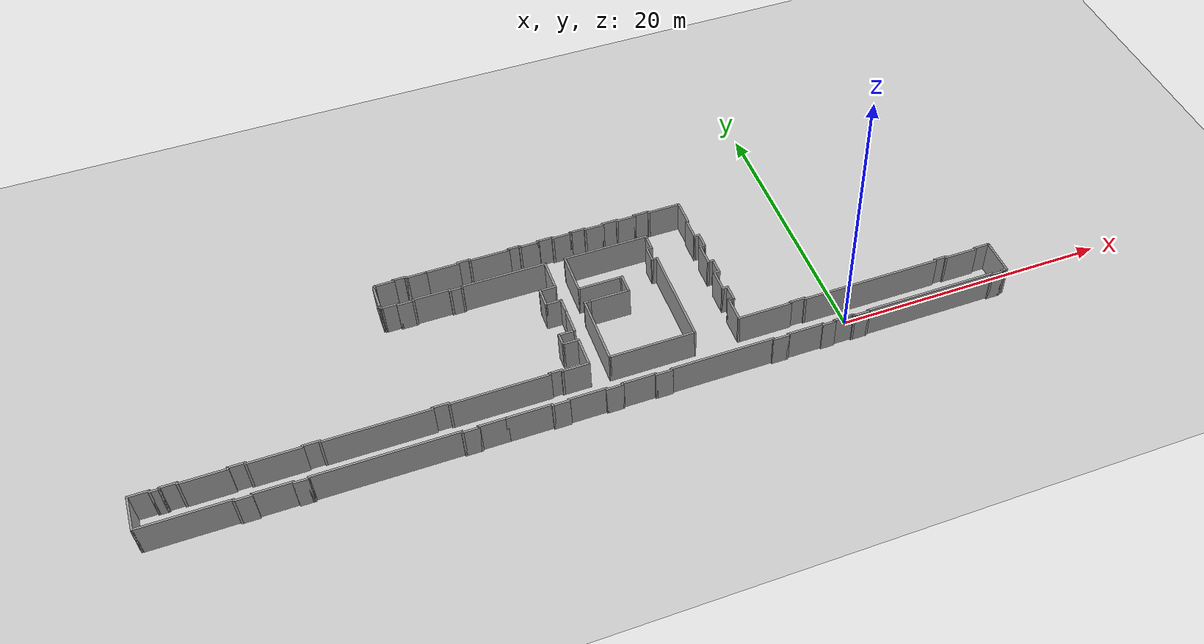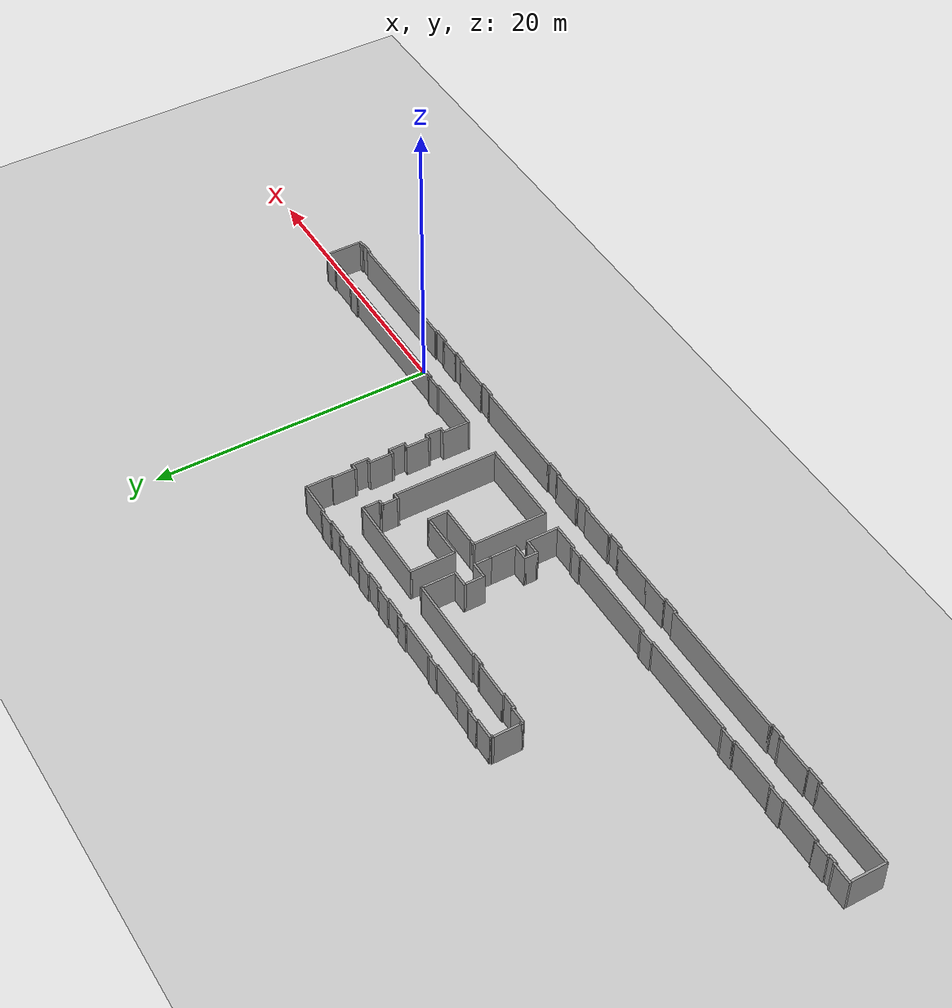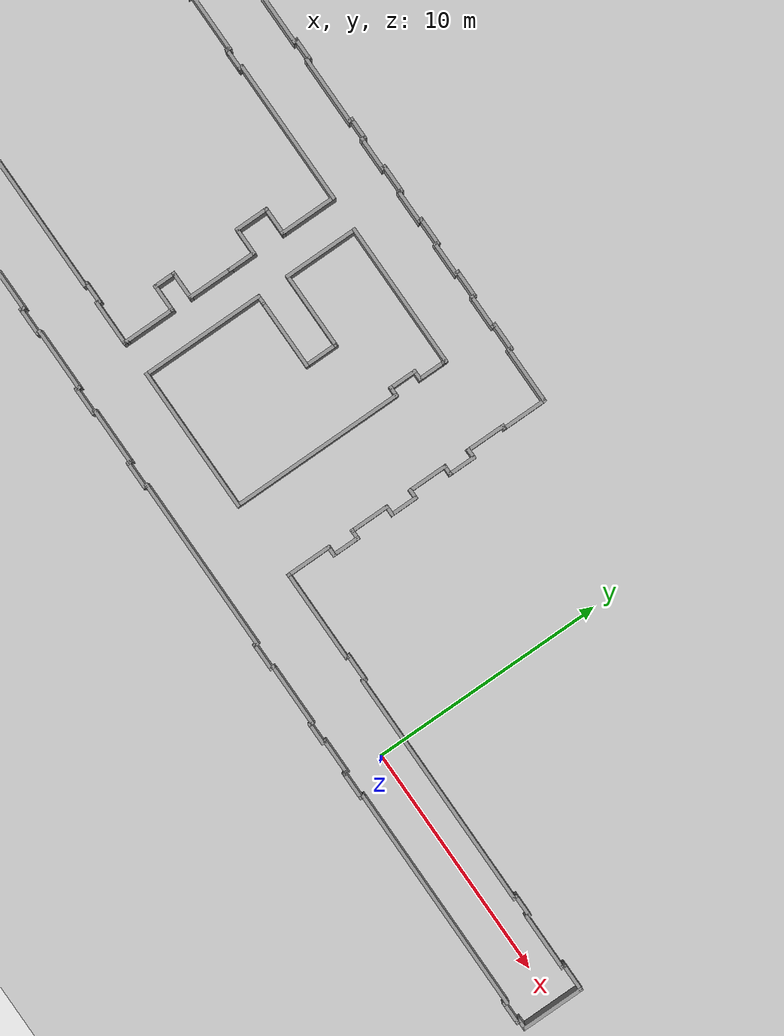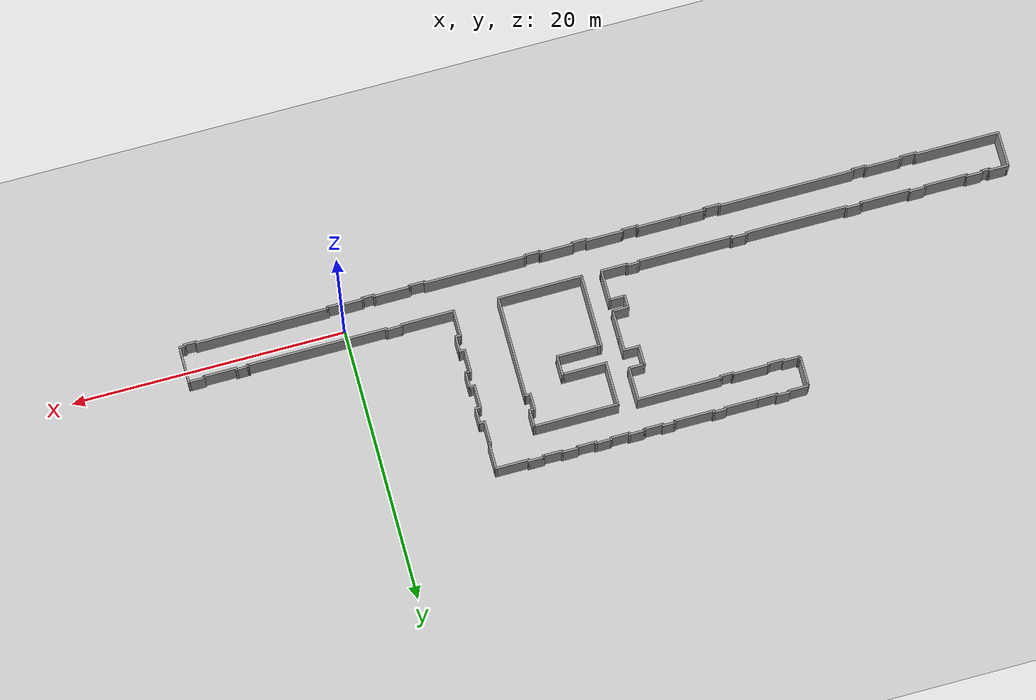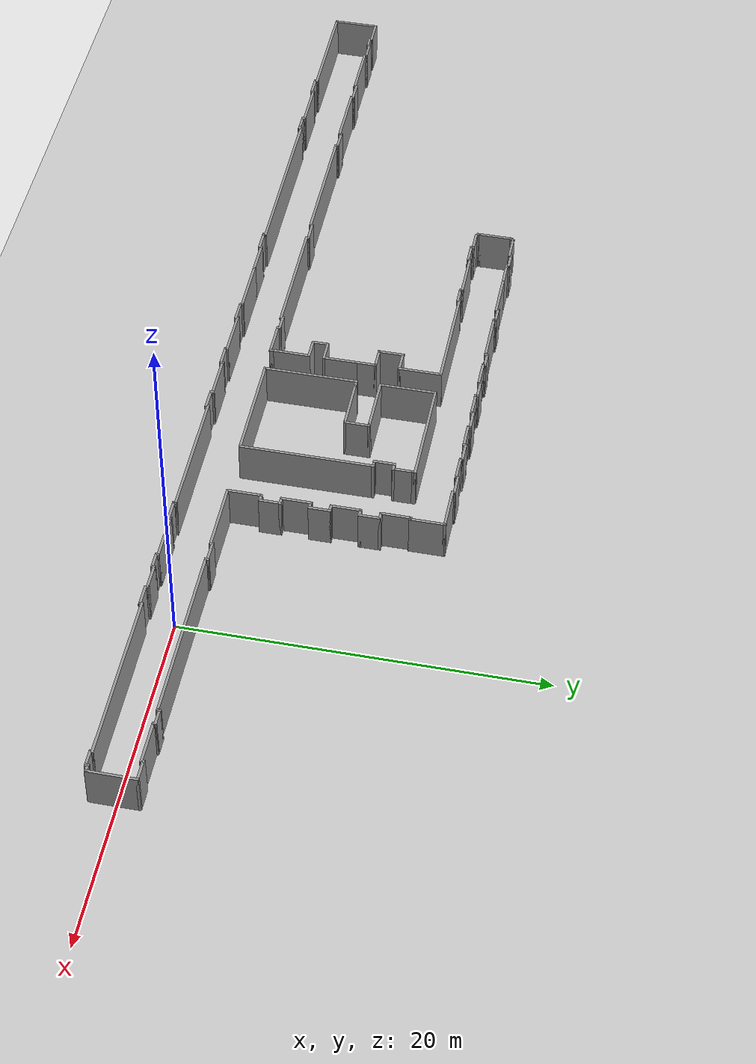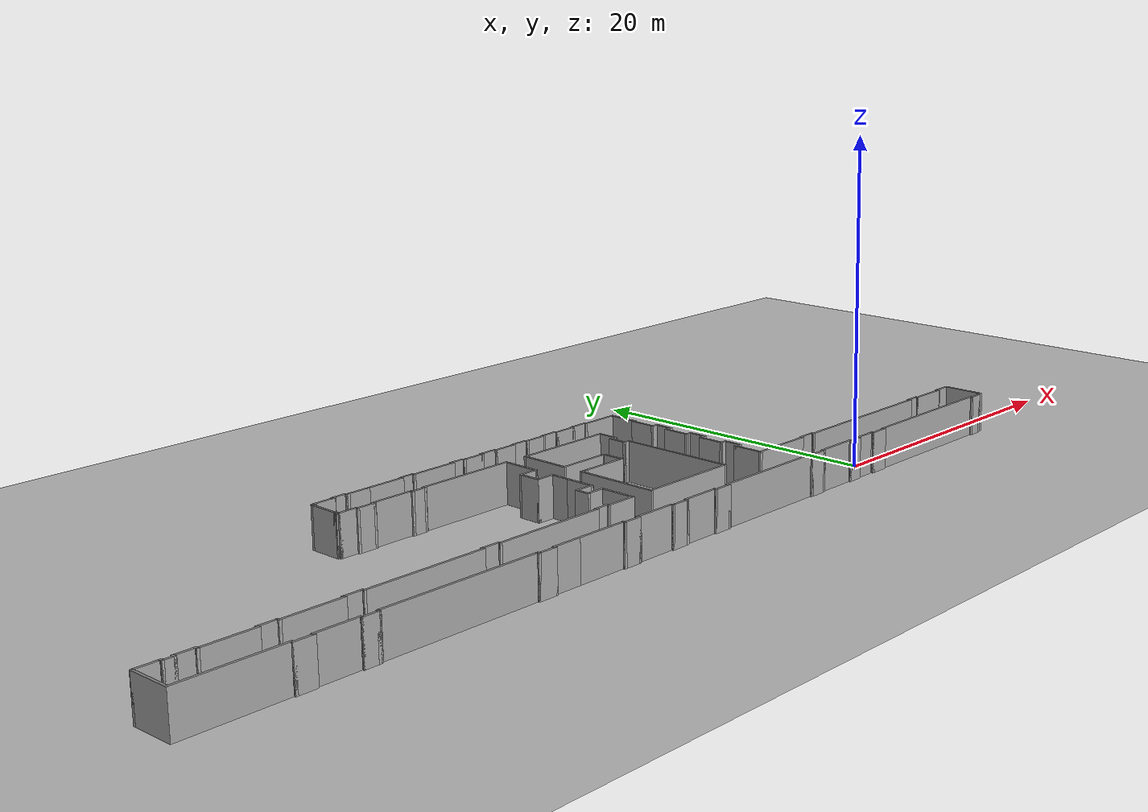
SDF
<sdf version="1.6">
 <world name="default">
  <light name="sun" type="directional">
   <pose>0 0 10 0 -0 0</pose>
   <diffuse>0.8 0.8 0.8 1</diffuse>
   <specular>0.1 0.1 0.1 1</specular>
   <attenuation>
    <range>1000</range>
    <constant>0.9</constant>
    <linear>0.01</linear>
    <quadratic>0.001</quadratic>
   </attenuation>
   <direction>-0.5 0.5 -1</direction>
  </light>
  <model name="ground_plane">
   <static>1</static>
   <link name="link">
    <collision name="collision">
     <geometry><plane><normal>0 0 1</normal><size>100 100</size></plane></geometry>
     <surface><friction><ode><mu>100</mu><mu2>50</mu2></ode></friction></surface>
    </collision>
    <visual name="visual">
     <cast_shadows>0</cast_shadows>
     <geometry><plane><normal>0 0 1</normal><size>100 100</size></plane></geometry>
     <material>
      <script><uri>file://media/materials/scripts/gazebo.material</uri><name>Gazebo/Grey</name></script>
     </material>
    </visual>
   </link>
  </model>
  <gravity>0 0 -9.8</gravity>
  <magnetic_field>6e-06 2.3e-05 -4.2e-05</magnetic_field>
  <atmosphere type="adiabatic"/>
  <physics name="default_physics" default="0" type="ode">
   <max_step_size>0.001</max_step_size>
   <real_time_factor>1</real_time_factor>
   <real_time_update_rate>1000</real_time_update_rate>
  </physics>
  <scene><ambient>0.4 0.4 0.4 1</ambient><background>0.7 0.7 0.7 1</background><shadows>1</shadows></scene>
  <spherical_coordinates>
   <surface_model>EARTH_WGS84</surface_model>
   <latitude_deg>0</latitude_deg>
   <longitude_deg>0</longitude_deg>
   <elevation>0</elevation>
   <heading_deg>0</heading_deg>
  </spherical_coordinates>
  <model name="hallway">
   <pose>-18.4373 5.74333 0 0 -0 0</pose>
   <link name="Wall_10">
    <collision name="Wall_10_Collision">
     <geometry><box><size>0.25 0.15 2.5</size></box></geometry>
     <pose>0 0 1.25 0 -0 0</pose>
    </collision>
    <visual name="Wall_10_Visual">
     <pose>0 0 1.25 0 -0 0</pose>
     <geometry><box><size>0.25 0.15 2.5</size></box></geometry>
     <material>
      <script><uri>file://media/materials/scripts/gazebo.material</uri><name>Gazebo/Grey</name></script>
      <ambient>1 1 1 1</ambient>
     </material>
    </visual>
    <pose>-20.275 -7.2 0 0 0 -1.5708</pose>
   </link>
   <link name="Wall_100">
    <collision name="Wall_100_Collision">
     <geometry><box><size>3 0.15 2.5</size></box></geometry>
     <pose>0 0 1.25 0 -0 0</pose>
    </collision>
    <visual name="Wall_100_Visual">
     <pose>0 0 1.25 0 -0 0</pose>
     <geometry><box><size>3 0.15 2.5</size></box></geometry>
     <material>
      <script><uri>file://media/materials/scripts/gazebo.material</uri><name>Gazebo/Grey</name></script>
      <ambient>1 1 1 1</ambient>
     </material>
    </visual>
    <pose>-3.6 7.15 0 0 -0 3.14159</pose>
   </link>
   <link name="Wall_101">
    <collision name="Wall_101_Collision">
     <geometry><box><size>0.25 0.15 2.5</size></box></geometry>
     <pose>0 0 1.25 0 -0 0</pose>
    </collision>
    <visual name="Wall_101_Visual">
     <pose>0 0 1.25 0 -0 0</pose>
     <geometry><box><size>0.25 0.15 2.5</size></box></geometry>
     <material>
      <script><uri>file://media/materials/scripts/gazebo.material</uri><name>Gazebo/Grey</name></script>
      <ambient>1 1 1 1</ambient>
     </material>
    </visual>
    <pose>-5.025 7.2 0 0 -0 1.5708</pose>
   </link>
   <link name="Wall_102">
    <collision name="Wall_102_Collision">
     <geometry><box><size>1 0.15 2.5</size></box></geometry>
     <pose>0 0 1.25 0 -0 0</pose>
    </collision>
    <visual name="Wall_102_Visual">
     <pose>0 0 1.25 0 -0 0</pose>
     <geometry><box><size>1 0.15 2.5</size></box></geometry>
     <material>
      <script><uri>file://media/materials/scripts/gazebo.material</uri><name>Gazebo/Grey</name></script>
      <ambient>1 1 1 1</ambient>
     </material>
    </visual>
    <pose>-5.45 7.25 0 0 -0 3.14159</pose>
   </link>
   <link name="Wall_103">
    <collision name="Wall_103_Collision">
     <geometry><box><size>0.25 0.15 2.5</size></box></geometry>
     <pose>0 0 1.25 0 -0 0</pose>
    </collision>
    <visual name="Wall_103_Visual">
     <pose>0 0 1.25 0 -0 0</pose>
     <geometry><box><size>0.25 0.15 2.5</size></box></geometry>
     <material>
      <script><uri>file://media/materials/scripts/gazebo.material</uri><name>Gazebo/Grey</name></script>
      <ambient>1 1 1 1</ambient>
     </material>
    </visual>
    <pose>-5.875 7.2 0 0 0 -1.5708</pose>
   </link>
   <link name="Wall_104">
    <collision name="Wall_104_Collision">
     <geometry><box><size>2.5 0.15 2.5</size></box></geometry>
     <pose>0 0 1.25 0 -0 0</pose>
    </collision>
    <visual name="Wall_104_Visual">
     <pose>0 0 1.25 0 -0 0</pose>
     <geometry><box><size>2.5 0.15 2.5</size></box></geometry>
     <material>
      <script><uri>file://media/materials/scripts/gazebo.material</uri><name>Gazebo/Grey</name></script>
      <ambient>1 1 1 1</ambient>
     </material>
    </visual>
    <pose>-7.05 7.15 0 0 -0 3.14159</pose>
   </link>
   <link name="Wall_106">
    <collision name="Wall_106_Collision">
     <geometry><box><size>1.5 0.15 2.5</size></box></geometry>
     <pose>0 0 1.25 0 -0 0</pose>
    </collision>
    <visual name="Wall_106_Visual">
     <pose>0 0 1.25 0 -0 0</pose>
     <geometry><box><size>1.5 0.15 2.5</size></box></geometry>
     <material>
      <script><uri>file://media/materials/scripts/gazebo.material</uri><name>Gazebo/Grey</name></script>
      <ambient>1 1 1 1</ambient>
     </material>
    </visual>
    <pose>-8.9 7.15 0 0 -0 3.14159</pose>
   </link>
   <link name="Wall_107">
    <collision name="Wall_107_Collision">
     <geometry><box><size>0.25 0.15 2.5</size></box></geometry>
     <pose>0 0 1.25 0 -0 0</pose>
    </collision>
    <visual name="Wall_107_Visual">
     <pose>0 0 1.25 0 -0 0</pose>
     <geometry><box><size>0.25 0.15 2.5</size></box></geometry>
     <material>
      <script><uri>file://media/materials/scripts/gazebo.material</uri><name>Gazebo/Grey</name></script>
      <ambient>1 1 1 1</ambient>
     </material>
    </visual>
    <pose>-9.625 7.15 0 0 -0 3.14159</pose>
   </link>
   <link name="Wall_108">
    <collision name="Wall_108_Collision">
     <geometry><box><size>0.25 0.15 2.5</size></box></geometry>
     <pose>0 0 1.25 0 -0 0</pose>
    </collision>
    <visual name="Wall_108_Visual">
     <pose>0 0 1.25 0 -0 0</pose>
     <geometry><box><size>0.25 0.15 2.5</size></box></geometry>
     <material>
      <script><uri>file://media/materials/scripts/gazebo.material</uri><name>Gazebo/Grey</name></script>
      <ambient>1 1 1 1</ambient>
     </material>
    </visual>
    <pose>-9.675 7.2 0 0 -0 1.5708</pose>
   </link>
   <link name="Wall_109">
    <collision name="Wall_109_Collision">
     <geometry><box><size>1 0.15 2.5</size></box></geometry>
     <pose>0 0 1.25 0 -0 0</pose>
    </collision>
    <visual name="Wall_109_Visual">
     <pose>0 0 1.25 0 -0 0</pose>
     <geometry><box><size>1 0.15 2.5</size></box></geometry>
     <material>
      <script><uri>file://media/materials/scripts/gazebo.material</uri><name>Gazebo/Grey</name></script>
      <ambient>1 1 1 1</ambient>
     </material>
    </visual>
    <pose>-10.1 7.25 0 0 -0 3.14159</pose>
   </link>
   <link name="Wall_11">
    <collision name="Wall_11_Collision">
     <geometry><box><size>1 0.15 2.5</size></box></geometry>
     <pose>0 0 1.25 0 -0 0</pose>
    </collision>
    <visual name="Wall_11_Visual">
     <pose>0 0 1.25 0 -0 0</pose>
     <geometry><box><size>1 0.15 2.5</size></box></geometry>
     <material>
      <script><uri>file://media/materials/scripts/gazebo.material</uri><name>Gazebo/Grey</name></script>
      <ambient>1 1 1 1</ambient>
     </material>
    </visual>
    <pose>-19.85 -7.25 0 0 -0 0</pose>
   </link>
   <link name="Wall_110">
    <collision name="Wall_110_Collision">
     <geometry><box><size>0.25 0.15 2.5</size></box></geometry>
     <pose>0 0 1.25 0 -0 0</pose>
    </collision>
    <visual name="Wall_110_Visual">
     <pose>0 0 1.25 0 -0 0</pose>
     <geometry><box><size>0.25 0.15 2.5</size></box></geometry>
     <material>
      <script><uri>file://media/materials/scripts/gazebo.material</uri><name>Gazebo/Grey</name></script>
      <ambient>1 1 1 1</ambient>
     </material>
    </visual>
    <pose>-10.525 7.2 0 0 0 -1.5708</pose>
   </link>
   <link name="Wall_111">
    <collision name="Wall_111_Collision">
     <geometry><box><size>1.5 0.15 2.5</size></box></geometry>
     <pose>0 0 1.25 0 -0 0</pose>
    </collision>
    <visual name="Wall_111_Visual">
     <pose>0 0 1.25 0 -0 0</pose>
     <geometry><box><size>1.5 0.15 2.5</size></box></geometry>
     <material>
      <script><uri>file://media/materials/scripts/gazebo.material</uri><name>Gazebo/Grey</name></script>
      <ambient>1 1 1 1</ambient>
     </material>
    </visual>
    <pose>-11.2 7.15 0 0 -0 3.14159</pose>
   </link>
   <link name="Wall_112">
    <collision name="Wall_112_Collision">
     <geometry><box><size>0.25 0.15 2.5</size></box></geometry>
     <pose>0 0 1.25 0 -0 0</pose>
    </collision>
    <visual name="Wall_112_Visual">
     <pose>0 0 1.25 0 -0 0</pose>
     <geometry><box><size>0.25 0.15 2.5</size></box></geometry>
     <material>
      <script><uri>file://media/materials/scripts/gazebo.material</uri><name>Gazebo/Grey</name></script>
      <ambient>1 1 1 1</ambient>
     </material>
    </visual>
    <pose>-11.875 7.1 0 0 0 -1.5708</pose>
   </link>
   <link name="Wall_113">
    <collision name="Wall_113_Collision">
     <geometry><box><size>0.25 0.15 2.5</size></box></geometry>
     <pose>0 0 1.25 0 -0 0</pose>
    </collision>
    <visual name="Wall_113_Visual">
     <pose>0 0 1.25 0 -0 0</pose>
     <geometry><box><size>0.25 0.15 2.5</size></box></geometry>
     <material>
      <script><uri>file://media/materials/scripts/gazebo.material</uri><name>Gazebo/Grey</name></script>
      <ambient>1 1 1 1</ambient>
     </material>
    </visual>
    <pose>-11.925 7.05 0 0 -0 3.14159</pose>
   </link>
   <link name="Wall_114">
    <collision name="Wall_114_Collision">
     <geometry><box><size>2.03478 0.15 2.5</size></box></geometry>
     <pose>0 0 1.25 0 -0 0</pose>
    </collision>
    <visual name="Wall_114_Visual">
     <pose>0 0 1.25 0 -0 0</pose>
     <geometry><box><size>2.03478 0.15 2.5</size></box></geometry>
     <material>
      <script><uri>file://media/materials/scripts/gazebo.material</uri><name>Gazebo/Grey</name></script>
      <ambient>1 1 1 1</ambient>
     </material>
    </visual>
    <pose>-11.975 6.10761 0 0 0 -1.5708</pose>
   </link>
   <link name="Wall_115">
    <collision name="Wall_115_Collision">
     <geometry><box><size>0.15 0.15 2.5</size></box></geometry>
     <pose>0 0 1.25 0 -0 0</pose>
    </collision>
    <visual name="Wall_115_Visual">
     <pose>0 0 1.25 0 -0 0</pose>
     <geometry><box><size>0.15 0.15 2.5</size></box></geometry>
     <material>
      <script><uri>file://media/materials/scripts/gazebo.material</uri><name>Gazebo/Grey</name></script>
      <ambient>1 1 1 1</ambient>
     </material>
    </visual>
    <pose>-11.975 5.16522 0 0 -0 0</pose>
   </link>
   <link name="Wall_12">
    <collision name="Wall_12_Collision">
     <geometry><box><size>0.25 0.15 2.5</size></box></geometry>
     <pose>0 0 1.25 0 -0 0</pose>
    </collision>
    <visual name="Wall_12_Visual">
     <pose>0 0 1.25 0 -0 0</pose>
     <geometry><box><size>0.25 0.15 2.5</size></box></geometry>
     <material>
      <script><uri>file://media/materials/scripts/gazebo.material</uri><name>Gazebo/Grey</name></script>
      <ambient>1 1 1 1</ambient>
     </material>
    </visual>
    <pose>-19.375 -7.25 0 0 -0 0</pose>
   </link>
   <link name="Wall_128">
    <collision name="Wall_128_Collision">
     <geometry><box><size>0.25 0.15 2.5</size></box></geometry>
     <pose>0 0 1.25 0 -0 0</pose>
    </collision>
    <visual name="Wall_128_Visual">
     <pose>0 0 1.25 0 -0 0</pose>
     <geometry><box><size>0.25 0.15 2.5</size></box></geometry>
     <material>
      <script><uri>file://media/materials/scripts/gazebo.material</uri><name>Gazebo/Grey</name></script>
      <ambient>1 1 1 1</ambient>
     </material>
    </visual>
    <pose>-11.975 5.11522 0 0 0 -1.5708</pose>
   </link>
   <link name="Wall_129">
    <collision name="Wall_129_Collision">
     <geometry><box><size>0.25 0.15 2.5</size></box></geometry>
     <pose>0 0 1.25 0 -0 0</pose>
    </collision>
    <visual name="Wall_129_Visual">
     <pose>0 0 1.25 0 -0 0</pose>
     <geometry><box><size>0.25 0.15 2.5</size></box></geometry>
     <material>
      <script><uri>file://media/materials/scripts/gazebo.material</uri><name>Gazebo/Grey</name></script>
      <ambient>1 1 1 1</ambient>
     </material>
    </visual>
    <pose>-11.925 5.06522 0 0 -0 0</pose>
   </link>
   <link name="Wall_13">
    <collision name="Wall_13_Collision">
     <geometry><box><size>0.25 0.15 2.5</size></box></geometry>
     <pose>0 0 1.25 0 -0 0</pose>
    </collision>
    <visual name="Wall_13_Visual">
     <pose>0 0 1.25 0 -0 0</pose>
     <geometry><box><size>0.25 0.15 2.5</size></box></geometry>
     <material>
      <script><uri>file://media/materials/scripts/gazebo.material</uri><name>Gazebo/Grey</name></script>
      <ambient>1 1 1 1</ambient>
     </material>
    </visual>
    <pose>-19.325 -7.2 0 0 -0 1.5708</pose>
   </link>
   <link name="Wall_130">
    <collision name="Wall_130_Collision">
     <geometry><box><size>0.25 0.15 2.5</size></box></geometry>
     <pose>0 0 1.25 0 -0 0</pose>
    </collision>
    <visual name="Wall_130_Visual">
     <pose>0 0 1.25 0 -0 0</pose>
     <geometry><box><size>0.25 0.15 2.5</size></box></geometry>
     <material>
      <script><uri>file://media/materials/scripts/gazebo.material</uri><name>Gazebo/Grey</name></script>
      <ambient>1 1 1 1</ambient>
     </material>
    </visual>
    <pose>-11.875 5.01522 0 0 0 -1.5708</pose>
   </link>
   <link name="Wall_131">
    <collision name="Wall_131_Collision">
     <geometry><box><size>1.25 0.15 2.5</size></box></geometry>
     <pose>0 0 1.25 0 -0 0</pose>
    </collision>
    <visual name="Wall_131_Visual">
     <pose>0 0 1.25 0 -0 0</pose>
     <geometry><box><size>1.25 0.15 2.5</size></box></geometry>
     <material>
      <script><uri>file://media/materials/scripts/gazebo.material</uri><name>Gazebo/Grey</name></script>
      <ambient>1 1 1 1</ambient>
     </material>
    </visual>
    <pose>-11.325 4.96522 0 0 -0 0</pose>
   </link>
   <link name="Wall_132">
    <collision name="Wall_132_Collision">
     <geometry><box><size>0.25 0.15 2.5</size></box></geometry>
     <pose>0 0 1.25 0 -0 0</pose>
    </collision>
    <visual name="Wall_132_Visual">
     <pose>0 0 1.25 0 -0 0</pose>
     <geometry><box><size>0.25 0.15 2.5</size></box></geometry>
     <material>
      <script><uri>file://media/materials/scripts/gazebo.material</uri><name>Gazebo/Grey</name></script>
      <ambient>1 1 1 1</ambient>
     </material>
    </visual>
    <pose>-10.775 4.91522 0 0 0 -1.5708</pose>
   </link>
   <link name="Wall_133">
    <collision name="Wall_133_Collision">
     <geometry><box><size>1.25 0.15 2.5</size></box></geometry>
     <pose>0 0 1.25 0 -0 0</pose>
    </collision>
    <visual name="Wall_133_Visual">
     <pose>0 0 1.25 0 -0 0</pose>
     <geometry><box><size>1.25 0.15 2.5</size></box></geometry>
     <material>
      <script><uri>file://media/materials/scripts/gazebo.material</uri><name>Gazebo/Grey</name></script>
      <ambient>1 1 1 1</ambient>
     </material>
    </visual>
    <pose>-10.225 4.86522 0 0 -0 0</pose>
   </link>
   <link name="Wall_134">
    <collision name="Wall_134_Collision">
     <geometry><box><size>0.25 0.15 2.5</size></box></geometry>
     <pose>0 0 1.25 0 -0 0</pose>
    </collision>
    <visual name="Wall_134_Visual">
     <pose>0 0 1.25 0 -0 0</pose>
     <geometry><box><size>0.25 0.15 2.5</size></box></geometry>
     <material>
      <script><uri>file://media/materials/scripts/gazebo.material</uri><name>Gazebo/Grey</name></script>
      <ambient>1 1 1 1</ambient>
     </material>
    </visual>
    <pose>-9.675 4.91522 0 0 -0 1.5708</pose>
   </link>
   <link name="Wall_135">
    <collision name="Wall_135_Collision">
     <geometry><box><size>2.75 0.15 2.5</size></box></geometry>
     <pose>0 0 1.25 0 -0 0</pose>
    </collision>
    <visual name="Wall_135_Visual">
     <pose>0 0 1.25 0 -0 0</pose>
     <geometry><box><size>2.75 0.15 2.5</size></box></geometry>
     <material>
      <script><uri>file://media/materials/scripts/gazebo.material</uri><name>Gazebo/Grey</name></script>
      <ambient>1 1 1 1</ambient>
     </material>
    </visual>
    <pose>-8.375 4.96522 0 0 -0 0</pose>
   </link>
   <link name="Wall_136">
    <collision name="Wall_136_Collision">
     <geometry><box><size>0.25 0.15 2.5</size></box></geometry>
     <pose>0 0 1.25 0 -0 0</pose>
    </collision>
    <visual name="Wall_136_Visual">
     <pose>0 0 1.25 0 -0 0</pose>
     <geometry><box><size>0.25 0.15 2.5</size></box></geometry>
     <material>
      <script><uri>file://media/materials/scripts/gazebo.material</uri><name>Gazebo/Grey</name></script>
      <ambient>1 1 1 1</ambient>
     </material>
    </visual>
    <pose>-7.075 4.91522 0 0 0 -1.5708</pose>
   </link>
   <link name="Wall_137">
    <collision name="Wall_137_Collision">
     <geometry><box><size>1 0.15 2.5</size></box></geometry>
     <pose>0 0 1.25 0 -0 0</pose>
    </collision>
    <visual name="Wall_137_Visual">
     <pose>0 0 1.25 0 -0 0</pose>
     <geometry><box><size>1 0.15 2.5</size></box></geometry>
     <material>
      <script><uri>file://media/materials/scripts/gazebo.material</uri><name>Gazebo/Grey</name></script>
      <ambient>1 1 1 1</ambient>
     </material>
    </visual>
    <pose>-6.65 4.86522 0 0 -0 0</pose>
   </link>
   <link name="Wall_138">
    <collision name="Wall_138_Collision">
     <geometry><box><size>0.25 0.15 2.5</size></box></geometry>
     <pose>0 0 1.25 0 -0 0</pose>
    </collision>
    <visual name="Wall_138_Visual">
     <pose>0 0 1.25 0 -0 0</pose>
     <geometry><box><size>0.25 0.15 2.5</size></box></geometry>
     <material>
      <script><uri>file://media/materials/scripts/gazebo.material</uri><name>Gazebo/Grey</name></script>
      <ambient>1 1 1 1</ambient>
     </material>
    </visual>
    <pose>-6.225 4.91522 0 0 -0 1.5708</pose>
   </link>
   <link name="Wall_139">
    <collision name="Wall_139_Collision">
     <geometry><box><size>6.25 0.15 2.5</size></box></geometry>
     <pose>0 0 1.25 0 -0 0</pose>
    </collision>
    <visual name="Wall_139_Visual">
     <pose>0 0 1.25 0 -0 0</pose>
     <geometry><box><size>6.25 0.15 2.5</size></box></geometry>
     <material>
      <script><uri>file://media/materials/scripts/gazebo.material</uri><name>Gazebo/Grey</name></script>
      <ambient>1 1 1 1</ambient>
     </material>
    </visual>
    <pose>-3.175 4.96522 0 0 -0 0</pose>
   </link>
   <link name="Wall_14">
    <collision name="Wall_14_Collision">
     <geometry><box><size>10 0.15 2.5</size></box></geometry>
     <pose>0 0 1.25 0 -0 0</pose>
    </collision>
    <visual name="Wall_14_Visual">
     <pose>0 0 1.25 0 -0 0</pose>
     <geometry><box><size>10 0.15 2.5</size></box></geometry>
     <material>
      <script><uri>file://media/materials/scripts/gazebo.material</uri><name>Gazebo/Grey</name></script>
      <ambient>1 1 1 1</ambient>
     </material>
    </visual>
    <pose>-14.4 -7.15 0 0 -0 0</pose>
   </link>
   <link name="Wall_140">
    <collision name="Wall_140_Collision">
     <geometry><box><size>2.5 0.15 2.5</size></box></geometry>
     <pose>0 0 1.25 0 -0 0</pose>
    </collision>
    <visual name="Wall_140_Visual">
     <pose>0 0 1.25 0 -0 0</pose>
     <geometry><box><size>2.5 0.15 2.5</size></box></geometry>
     <material>
      <script><uri>file://media/materials/scripts/gazebo.material</uri><name>Gazebo/Grey</name></script>
      <ambient>1 1 1 1</ambient>
     </material>
    </visual>
    <pose>-0.125 3.79022 0 0 0 -1.5708</pose>
   </link>
   <link name="Wall_141">
    <collision name="Wall_141_Collision">
     <geometry><box><size>1.25 0.15 2.5</size></box></geometry>
     <pose>0 0 1.25 0 -0 0</pose>
    </collision>
    <visual name="Wall_141_Visual">
     <pose>0 0 1.25 0 -0 0</pose>
     <geometry><box><size>1.25 0.15 2.5</size></box></geometry>
     <material>
      <script><uri>file://media/materials/scripts/gazebo.material</uri><name>Gazebo/Grey</name></script>
      <ambient>1 1 1 1</ambient>
     </material>
    </visual>
    <pose>-0.675 2.61522 0 0 -0 3.14159</pose>
   </link>
   <link name="Wall_142">
    <collision name="Wall_142_Collision">
     <geometry><box><size>1.5 0.15 2.5</size></box></geometry>
     <pose>0 0 1.25 0 -0 0</pose>
    </collision>
    <visual name="Wall_142_Visual">
     <pose>0 0 1.25 0 -0 0</pose>
     <geometry><box><size>1.5 0.15 2.5</size></box></geometry>
     <material>
      <script><uri>file://media/materials/scripts/gazebo.material</uri><name>Gazebo/Grey</name></script>
      <ambient>1 1 1 1</ambient>
     </material>
    </visual>
    <pose>-1.225 1.94022 0 0 0 -1.5708</pose>
   </link>
   <link name="Wall_143">
    <collision name="Wall_143_Collision">
     <geometry><box><size>1.25 0.15 2.5</size></box></geometry>
     <pose>0 0 1.25 0 -0 0</pose>
    </collision>
    <visual name="Wall_143_Visual">
     <pose>0 0 1.25 0 -0 0</pose>
     <geometry><box><size>1.25 0.15 2.5</size></box></geometry>
     <material>
      <script><uri>file://media/materials/scripts/gazebo.material</uri><name>Gazebo/Grey</name></script>
      <ambient>1 1 1 1</ambient>
     </material>
    </visual>
    <pose>-0.675 1.26522 0 0 -0 0</pose>
   </link>
   <link name="Wall_144">
    <collision name="Wall_144_Collision">
     <geometry><box><size>1.25 0.15 2.5</size></box></geometry>
     <pose>0 0 1.25 0 -0 0</pose>
    </collision>
    <visual name="Wall_144_Visual">
     <pose>0 0 1.25 0 -0 0</pose>
     <geometry><box><size>1.25 0.15 2.5</size></box></geometry>
     <material>
      <script><uri>file://media/materials/scripts/gazebo.material</uri><name>Gazebo/Grey</name></script>
      <ambient>1 1 1 1</ambient>
     </material>
    </visual>
    <pose>-0.125 0.715217 0 0 0 -1.5708</pose>
   </link>
   <link name="Wall_146">
    <collision name="Wall_146_Collision">
     <geometry><box><size>2 0.15 2.5</size></box></geometry>
     <pose>0 0 1.25 0 -0 0</pose>
    </collision>
    <visual name="Wall_146_Visual">
     <pose>0 0 1.25 0 -0 0</pose>
     <geometry><box><size>2 0.15 2.5</size></box></geometry>
     <material>
      <script><uri>file://media/materials/scripts/gazebo.material</uri><name>Gazebo/Grey</name></script>
      <ambient>1 1 1 1</ambient>
     </material>
    </visual>
    <pose>-0.125 -0.759783 0 0 0 -1.5708</pose>
   </link>
   <link name="Wall_147">
    <collision name="Wall_147_Collision">
     <geometry><box><size>1.25 0.15 2.5</size></box></geometry>
     <pose>0 0 1.25 0 -0 0</pose>
    </collision>
    <visual name="Wall_147_Visual">
     <pose>0 0 1.25 0 -0 0</pose>
     <geometry><box><size>1.25 0.15 2.5</size></box></geometry>
     <material>
      <script><uri>file://media/materials/scripts/gazebo.material</uri><name>Gazebo/Grey</name></script>
      <ambient>1 1 1 1</ambient>
     </material>
    </visual>
    <pose>-0.675 -1.68478 0 0 -0 3.14159</pose>
   </link>
   <link name="Wall_148">
    <collision name="Wall_148_Collision">
     <geometry><box><size>1 0.15 2.5</size></box></geometry>
     <pose>0 0 1.25 0 -0 0</pose>
    </collision>
    <visual name="Wall_148_Visual">
     <pose>0 0 1.25 0 -0 0</pose>
     <geometry><box><size>1 0.15 2.5</size></box></geometry>
     <material>
      <script><uri>file://media/materials/scripts/gazebo.material</uri><name>Gazebo/Grey</name></script>
      <ambient>1 1 1 1</ambient>
     </material>
    </visual>
    <pose>-1.225 -2.10978 0 0 0 -1.5708</pose>
   </link>
   <link name="Wall_15">
    <collision name="Wall_15_Collision">
     <geometry><box><size>0.25 0.15 2.5</size></box></geometry>
     <pose>0 0 1.25 0 -0 0</pose>
    </collision>
    <visual name="Wall_15_Visual">
     <pose>0 0 1.25 0 -0 0</pose>
     <geometry><box><size>0.25 0.15 2.5</size></box></geometry>
     <material>
      <script><uri>file://media/materials/scripts/gazebo.material</uri><name>Gazebo/Grey</name></script>
      <ambient>1 1 1 1</ambient>
     </material>
    </visual>
    <pose>-9.475 -7.2 0 0 0 -1.5708</pose>
   </link>
   <link name="Wall_156">
    <collision name="Wall_156_Collision">
     <geometry><box><size>1.25 0.15 2.5</size></box></geometry>
     <pose>0 0 1.25 0 -0 0</pose>
    </collision>
    <visual name="Wall_156_Visual">
     <pose>0 0 1.25 0 -0 0</pose>
     <geometry><box><size>1.25 0.15 2.5</size></box></geometry>
     <material>
      <script><uri>file://media/materials/scripts/gazebo.material</uri><name>Gazebo/Grey</name></script>
      <ambient>1 1 1 1</ambient>
     </material>
    </visual>
    <pose>-0.675 -2.53478 0 0 -0 0</pose>
   </link>
   <link name="Wall_157">
    <collision name="Wall_157_Collision">
     <geometry><box><size>2.25 0.15 2.5</size></box></geometry>
     <pose>0 0 1.25 0 -0 0</pose>
    </collision>
    <visual name="Wall_157_Visual">
     <pose>0 0 1.25 0 -0 0</pose>
     <geometry><box><size>2.25 0.15 2.5</size></box></geometry>
     <material>
      <script><uri>file://media/materials/scripts/gazebo.material</uri><name>Gazebo/Grey</name></script>
      <ambient>1 1 1 1</ambient>
     </material>
    </visual>
    <pose>-0.125 -3.58478 0 0 0 -1.5708</pose>
   </link>
   <link name="Wall_158">
    <collision name="Wall_158_Collision">
     <geometry><box><size>0.25 0.15 2.5</size></box></geometry>
     <pose>0 0 1.25 0 -0 0</pose>
    </collision>
    <visual name="Wall_158_Visual">
     <pose>0 0 1.25 0 -0 0</pose>
     <geometry><box><size>0.25 0.15 2.5</size></box></geometry>
     <material>
      <script><uri>file://media/materials/scripts/gazebo.material</uri><name>Gazebo/Grey</name></script>
      <ambient>1 1 1 1</ambient>
     </material>
    </visual>
    <pose>-0.125 -4.68478 0 0 0 -1.5708</pose>
   </link>
   <link name="Wall_159">
    <collision name="Wall_159_Collision">
     <geometry><box><size>2 0.15 2.5</size></box></geometry>
     <pose>0 0 1.25 0 -0 0</pose>
    </collision>
    <visual name="Wall_159_Visual">
     <pose>0 0 1.25 0 -0 0</pose>
     <geometry><box><size>2 0.15 2.5</size></box></geometry>
     <material>
      <script><uri>file://media/materials/scripts/gazebo.material</uri><name>Gazebo/Grey</name></script>
      <ambient>1 1 1 1</ambient>
     </material>
    </visual>
    <pose>-1.05 -4.73478 0 0 -0 3.14159</pose>
   </link>
   <link name="Wall_16">
    <collision name="Wall_16_Collision">
     <geometry><box><size>1.25 0.15 2.5</size></box></geometry>
     <pose>0 0 1.25 0 -0 0</pose>
    </collision>
    <visual name="Wall_16_Visual">
     <pose>0 0 1.25 0 -0 0</pose>
     <geometry><box><size>1.25 0.15 2.5</size></box></geometry>
     <material>
      <script><uri>file://media/materials/scripts/gazebo.material</uri><name>Gazebo/Grey</name></script>
      <ambient>1 1 1 1</ambient>
     </material>
    </visual>
    <pose>-8.925 -7.25 0 0 -0 0</pose>
   </link>
   <link name="Wall_160">
    <collision name="Wall_160_Collision">
     <geometry><box><size>0.25 0.15 2.5</size></box></geometry>
     <pose>0 0 1.25 0 -0 0</pose>
    </collision>
    <visual name="Wall_160_Visual">
     <pose>0 0 1.25 0 -0 0</pose>
     <geometry><box><size>0.25 0.15 2.5</size></box></geometry>
     <material>
      <script><uri>file://media/materials/scripts/gazebo.material</uri><name>Gazebo/Grey</name></script>
      <ambient>1 1 1 1</ambient>
     </material>
    </visual>
    <pose>-1.975 -4.68478 0 0 -0 1.5708</pose>
   </link>
   <link name="Wall_161">
    <collision name="Wall_161_Collision">
     <geometry><box><size>1 0.15 2.5</size></box></geometry>
     <pose>0 0 1.25 0 -0 0</pose>
    </collision>
    <visual name="Wall_161_Visual">
     <pose>0 0 1.25 0 -0 0</pose>
     <geometry><box><size>1 0.15 2.5</size></box></geometry>
     <material>
      <script><uri>file://media/materials/scripts/gazebo.material</uri><name>Gazebo/Grey</name></script>
      <ambient>1 1 1 1</ambient>
     </material>
    </visual>
    <pose>-2.4 -4.63478 0 0 -0 3.14159</pose>
   </link>
   <link name="Wall_162">
    <collision name="Wall_162_Collision">
     <geometry><box><size>0.25 0.15 2.5</size></box></geometry>
     <pose>0 0 1.25 0 -0 0</pose>
    </collision>
    <visual name="Wall_162_Visual">
     <pose>0 0 1.25 0 -0 0</pose>
     <geometry><box><size>0.25 0.15 2.5</size></box></geometry>
     <material>
      <script><uri>file://media/materials/scripts/gazebo.material</uri><name>Gazebo/Grey</name></script>
      <ambient>1 1 1 1</ambient>
     </material>
    </visual>
    <pose>-2.825 -4.68478 0 0 0 -1.5708</pose>
   </link>
   <link name="Wall_163">
    <collision name="Wall_163_Collision">
     <geometry><box><size>7 0.15 2.5</size></box></geometry>
     <pose>0 0 1.25 0 -0 0</pose>
    </collision>
    <visual name="Wall_163_Visual">
     <pose>0 0 1.25 0 -0 0</pose>
     <geometry><box><size>7 0.15 2.5</size></box></geometry>
     <material>
      <script><uri>file://media/materials/scripts/gazebo.material</uri><name>Gazebo/Grey</name></script>
      <ambient>1 1 1 1</ambient>
     </material>
    </visual>
    <pose>-6.25 -4.73478 0 0 -0 3.14159</pose>
   </link>
   <link name="Wall_164">
    <collision name="Wall_164_Collision">
     <geometry><box><size>0.25 0.15 2.5</size></box></geometry>
     <pose>0 0 1.25 0 -0 0</pose>
    </collision>
    <visual name="Wall_164_Visual">
     <pose>0 0 1.25 0 -0 0</pose>
     <geometry><box><size>0.25 0.15 2.5</size></box></geometry>
     <material>
      <script><uri>file://media/materials/scripts/gazebo.material</uri><name>Gazebo/Grey</name></script>
      <ambient>1 1 1 1</ambient>
     </material>
    </visual>
    <pose>-9.675 -4.68478 0 0 -0 1.5708</pose>
   </link>
   <link name="Wall_165">
    <collision name="Wall_165_Collision">
     <geometry><box><size>1.25 0.15 2.5</size></box></geometry>
     <pose>0 0 1.25 0 -0 0</pose>
    </collision>
    <visual name="Wall_165_Visual">
     <pose>0 0 1.25 0 -0 0</pose>
     <geometry><box><size>1.25 0.15 2.5</size></box></geometry>
     <material>
      <script><uri>file://media/materials/scripts/gazebo.material</uri><name>Gazebo/Grey</name></script>
      <ambient>1 1 1 1</ambient>
     </material>
    </visual>
    <pose>-10.225 -4.63478 0 0 -0 3.14159</pose>
   </link>
   <link name="Wall_166">
    <collision name="Wall_166_Collision">
     <geometry><box><size>0.25 0.15 2.5</size></box></geometry>
     <pose>0 0 1.25 0 -0 0</pose>
    </collision>
    <visual name="Wall_166_Visual">
     <pose>0 0 1.25 0 -0 0</pose>
     <geometry><box><size>0.25 0.15 2.5</size></box></geometry>
     <material>
      <script><uri>file://media/materials/scripts/gazebo.material</uri><name>Gazebo/Grey</name></script>
      <ambient>1 1 1 1</ambient>
     </material>
    </visual>
    <pose>-10.775 -4.68478 0 0 0 -1.5708</pose>
   </link>
   <link name="Wall_167">
    <collision name="Wall_167_Collision">
     <geometry><box><size>7.5 0.15 2.5</size></box></geometry>
     <pose>0 0 1.25 0 -0 0</pose>
    </collision>
    <visual name="Wall_167_Visual">
     <pose>0 0 1.25 0 -0 0</pose>
     <geometry><box><size>7.5 0.15 2.5</size></box></geometry>
     <material>
      <script><uri>file://media/materials/scripts/gazebo.material</uri><name>Gazebo/Grey</name></script>
      <ambient>1 1 1 1</ambient>
     </material>
    </visual>
    <pose>-14.45 -4.73478 0 0 -0 3.14159</pose>
   </link>
   <link name="Wall_168">
    <collision name="Wall_168_Collision">
     <geometry><box><size>0.25 0.15 2.5</size></box></geometry>
     <pose>0 0 1.25 0 -0 0</pose>
    </collision>
    <visual name="Wall_168_Visual">
     <pose>0 0 1.25 0 -0 0</pose>
     <geometry><box><size>0.25 0.15 2.5</size></box></geometry>
     <material>
      <script><uri>file://media/materials/scripts/gazebo.material</uri><name>Gazebo/Grey</name></script>
      <ambient>1 1 1 1</ambient>
     </material>
    </visual>
    <pose>-18.125 -4.68478 0 0 -0 1.5708</pose>
   </link>
   <link name="Wall_169">
    <collision name="Wall_169_Collision">
     <geometry><box><size>1.25 0.15 2.5</size></box></geometry>
     <pose>0 0 1.25 0 -0 0</pose>
    </collision>
    <visual name="Wall_169_Visual">
     <pose>0 0 1.25 0 -0 0</pose>
     <geometry><box><size>1.25 0.15 2.5</size></box></geometry>
     <material>
      <script><uri>file://media/materials/scripts/gazebo.material</uri><name>Gazebo/Grey</name></script>
      <ambient>1 1 1 1</ambient>
     </material>
    </visual>
    <pose>-18.675 -4.63478 0 0 -0 3.14159</pose>
   </link>
   <link name="Wall_17">
    <collision name="Wall_17_Collision">
     <geometry><box><size>0.25 0.15 2.5</size></box></geometry>
     <pose>0 0 1.25 0 -0 0</pose>
    </collision>
    <visual name="Wall_17_Visual">
     <pose>0 0 1.25 0 -0 0</pose>
     <geometry><box><size>0.25 0.15 2.5</size></box></geometry>
     <material>
      <script><uri>file://media/materials/scripts/gazebo.material</uri><name>Gazebo/Grey</name></script>
      <ambient>1 1 1 1</ambient>
     </material>
    </visual>
    <pose>-8.375 -7.2 0 0 -0 1.5708</pose>
   </link>
   <link name="Wall_170">
    <collision name="Wall_170_Collision">
     <geometry><box><size>0.25 0.15 2.5</size></box></geometry>
     <pose>0 0 1.25 0 -0 0</pose>
    </collision>
    <visual name="Wall_170_Visual">
     <pose>0 0 1.25 0 -0 0</pose>
     <geometry><box><size>0.25 0.15 2.5</size></box></geometry>
     <material>
      <script><uri>file://media/materials/scripts/gazebo.material</uri><name>Gazebo/Grey</name></script>
      <ambient>1 1 1 1</ambient>
     </material>
    </visual>
    <pose>-19.225 -4.68478 0 0 0 -1.5708</pose>
   </link>
   <link name="Wall_171">
    <collision name="Wall_171_Collision">
     <geometry><box><size>3.75 0.15 2.5</size></box></geometry>
     <pose>0 0 1.25 0 -0 0</pose>
    </collision>
    <visual name="Wall_171_Visual">
     <pose>0 0 1.25 0 -0 0</pose>
     <geometry><box><size>3.75 0.15 2.5</size></box></geometry>
     <material>
      <script><uri>file://media/materials/scripts/gazebo.material</uri><name>Gazebo/Grey</name></script>
      <ambient>1 1 1 1</ambient>
     </material>
    </visual>
    <pose>-21.025 -4.73478 0 0 -0 3.14159</pose>
   </link>
   <link name="Wall_172">
    <collision name="Wall_172_Collision">
     <geometry><box><size>0.25 0.15 2.5</size></box></geometry>
     <pose>0 0 1.25 0 -0 0</pose>
    </collision>
    <visual name="Wall_172_Visual">
     <pose>0 0 1.25 0 -0 0</pose>
     <geometry><box><size>0.25 0.15 2.5</size></box></geometry>
     <material>
      <script><uri>file://media/materials/scripts/gazebo.material</uri><name>Gazebo/Grey</name></script>
      <ambient>1 1 1 1</ambient>
     </material>
    </visual>
    <pose>-22.825 -4.68478 0 0 -0 1.5708</pose>
   </link>
   <link name="Wall_173">
    <collision name="Wall_173_Collision">
     <geometry><box><size>1.25 0.15 2.5</size></box></geometry>
     <pose>0 0 1.25 0 -0 0</pose>
    </collision>
    <visual name="Wall_173_Visual">
     <pose>0 0 1.25 0 -0 0</pose>
     <geometry><box><size>1.25 0.15 2.5</size></box></geometry>
     <material>
      <script><uri>file://media/materials/scripts/gazebo.material</uri><name>Gazebo/Grey</name></script>
      <ambient>1 1 1 1</ambient>
     </material>
    </visual>
    <pose>-23.375 -4.63478 0 0 -0 3.14159</pose>
   </link>
   <link name="Wall_174">
    <collision name="Wall_174_Collision">
     <geometry><box><size>0.25 0.15 2.5</size></box></geometry>
     <pose>0 0 1.25 0 -0 0</pose>
    </collision>
    <visual name="Wall_174_Visual">
     <pose>0 0 1.25 0 -0 0</pose>
     <geometry><box><size>0.25 0.15 2.5</size></box></geometry>
     <material>
      <script><uri>file://media/materials/scripts/gazebo.material</uri><name>Gazebo/Grey</name></script>
      <ambient>1 1 1 1</ambient>
     </material>
    </visual>
    <pose>-23.925 -4.68478 0 0 0 -1.5708</pose>
   </link>
   <link name="Wall_175">
    <collision name="Wall_175_Collision">
     <geometry><box><size>3.25 0.15 2.5</size></box></geometry>
     <pose>0 0 1.25 0 -0 0</pose>
    </collision>
    <visual name="Wall_175_Visual">
     <pose>0 0 1.25 0 -0 0</pose>
     <geometry><box><size>3.25 0.15 2.5</size></box></geometry>
     <material>
      <script><uri>file://media/materials/scripts/gazebo.material</uri><name>Gazebo/Grey</name></script>
      <ambient>1 1 1 1</ambient>
     </material>
    </visual>
    <pose>-25.475 -4.73478 0 0 -0 3.14159</pose>
   </link>
   <link name="Wall_176">
    <collision name="Wall_176_Collision">
     <geometry><box><size>0.25 0.15 2.5</size></box></geometry>
     <pose>0 0 1.25 0 -0 0</pose>
    </collision>
    <visual name="Wall_176_Visual">
     <pose>0 0 1.25 0 -0 0</pose>
     <geometry><box><size>0.25 0.15 2.5</size></box></geometry>
     <material>
      <script><uri>file://media/materials/scripts/gazebo.material</uri><name>Gazebo/Grey</name></script>
      <ambient>1 1 1 1</ambient>
     </material>
    </visual>
    <pose>-27.025 -4.68478 0 0 -0 1.5708</pose>
   </link>
   <link name="Wall_177">
    <collision name="Wall_177_Collision">
     <geometry><box><size>1.25 0.15 2.5</size></box></geometry>
     <pose>0 0 1.25 0 -0 0</pose>
    </collision>
    <visual name="Wall_177_Visual">
     <pose>0 0 1.25 0 -0 0</pose>
     <geometry><box><size>1.25 0.15 2.5</size></box></geometry>
     <material>
      <script><uri>file://media/materials/scripts/gazebo.material</uri><name>Gazebo/Grey</name></script>
      <ambient>1 1 1 1</ambient>
     </material>
    </visual>
    <pose>-27.575 -4.63478 0 0 -0 3.14159</pose>
   </link>
   <link name="Wall_178">
    <collision name="Wall_178_Collision">
     <geometry><box><size>0.25 0.15 2.5</size></box></geometry>
     <pose>0 0 1.25 0 -0 0</pose>
    </collision>
    <visual name="Wall_178_Visual">
     <pose>0 0 1.25 0 -0 0</pose>
     <geometry><box><size>0.25 0.15 2.5</size></box></geometry>
     <material>
      <script><uri>file://media/materials/scripts/gazebo.material</uri><name>Gazebo/Grey</name></script>
      <ambient>1 1 1 1</ambient>
     </material>
    </visual>
    <pose>-28.125 -4.68478 0 0 0 -1.5708</pose>
   </link>
   <link name="Wall_179">
    <collision name="Wall_179_Collision">
     <geometry><box><size>0.75 0.15 2.5</size></box></geometry>
     <pose>0 0 1.25 0 -0 0</pose>
    </collision>
    <visual name="Wall_179_Visual">
     <pose>0 0 1.25 0 -0 0</pose>
     <geometry><box><size>0.75 0.15 2.5</size></box></geometry>
     <material>
      <script><uri>file://media/materials/scripts/gazebo.material</uri><name>Gazebo/Grey</name></script>
      <ambient>1 1 1 1</ambient>
     </material>
    </visual>
    <pose>-28.425 -4.73478 0 0 -0 3.14159</pose>
   </link>
   <link name="Wall_18">
    <collision name="Wall_18_Collision">
     <geometry><box><size>2 0.15 2.5</size></box></geometry>
     <pose>0 0 1.25 0 -0 0</pose>
    </collision>
    <visual name="Wall_18_Visual">
     <pose>0 0 1.25 0 -0 0</pose>
     <geometry><box><size>2 0.15 2.5</size></box></geometry>
     <material>
      <script><uri>file://media/materials/scripts/gazebo.material</uri><name>Gazebo/Grey</name></script>
      <ambient>1 1 1 1</ambient>
     </material>
    </visual>
    <pose>-7.45 -7.15 0 0 -0 0</pose>
   </link>
   <link name="Wall_180">
    <collision name="Wall_180_Collision">
     <geometry><box><size>0.25 0.15 2.5</size></box></geometry>
     <pose>0 0 1.25 0 -0 0</pose>
    </collision>
    <visual name="Wall_180_Visual">
     <pose>0 0 1.25 0 -0 0</pose>
     <geometry><box><size>0.25 0.15 2.5</size></box></geometry>
     <material>
      <script><uri>file://media/materials/scripts/gazebo.material</uri><name>Gazebo/Grey</name></script>
      <ambient>1 1 1 1</ambient>
     </material>
    </visual>
    <pose>-28.725 -4.68478 0 0 -0 1.5708</pose>
   </link>
   <link name="Wall_181">
    <collision name="Wall_181_Collision">
     <geometry><box><size>1.5 0.15 2.5</size></box></geometry>
     <pose>0 0 1.25 0 -0 0</pose>
    </collision>
    <visual name="Wall_181_Visual">
     <pose>0 0 1.25 0 -0 0</pose>
     <geometry><box><size>1.5 0.15 2.5</size></box></geometry>
     <material>
      <script><uri>file://media/materials/scripts/gazebo.material</uri><name>Gazebo/Grey</name></script>
      <ambient>1 1 1 1</ambient>
     </material>
    </visual>
    <pose>-29.4 -4.63478 0 0 -0 3.14159</pose>
   </link>
   <link name="Wall_182">
    <collision name="Wall_182_Collision">
     <geometry><box><size>2.66522 0.15 2.5</size></box></geometry>
     <pose>0 0 1.25 0 -0 0</pose>
    </collision>
    <visual name="Wall_182_Visual">
     <pose>0 0 1.25 0 -0 0</pose>
     <geometry><box><size>2.66522 0.15 2.5</size></box></geometry>
     <material>
      <script><uri>file://media/materials/scripts/gazebo.material</uri><name>Gazebo/Grey</name></script>
      <ambient>1 1 1 1</ambient>
     </material>
    </visual>
    <pose>-30.075 -5.89239 0 0 0 -1.5708</pose>
   </link>
   <link name="Wall_184">
    <collision name="Wall_184_Collision">
     <geometry><box><size>6.25 0.15 2.5</size></box></geometry>
     <pose>0 0 1.25 0 -0 0</pose>
    </collision>
    <visual name="Wall_184_Visual">
     <pose>0 0 1.25 0 -0 0</pose>
     <geometry><box><size>6.25 0.15 2.5</size></box></geometry>
     <material>
      <script><uri>file://media/materials/scripts/gazebo.material</uri><name>Gazebo/Grey</name></script>
      <ambient>1 1 1 1</ambient>
     </material>
    </visual>
    <pose>4.38892 -4.72399 0 0 -0 0</pose>
   </link>
   <link name="Wall_185">
    <collision name="Wall_185_Collision">
     <geometry><box><size>7.5 0.15 2.5</size></box></geometry>
     <pose>0 0 1.25 0 -0 0</pose>
    </collision>
    <visual name="Wall_185_Visual">
     <pose>0 0 1.25 0 -0 0</pose>
     <geometry><box><size>7.5 0.15 2.5</size></box></geometry>
     <material>
      <script><uri>file://media/materials/scripts/gazebo.material</uri><name>Gazebo/Grey</name></script>
      <ambient>1 1 1 1</ambient>
     </material>
    </visual>
    <pose>7.43892 -1.04899 0 0 -0 1.5708</pose>
   </link>
   <link name="Wall_187">
    <collision name="Wall_187_Collision">
     <geometry><box><size>0.5 0.15 2.5</size></box></geometry>
     <pose>0 0 1.25 0 -0 0</pose>
    </collision>
    <visual name="Wall_187_Visual">
     <pose>0 0 1.25 0 -0 0</pose>
     <geometry><box><size>0.5 0.15 2.5</size></box></geometry>
     <material>
      <script><uri>file://media/materials/scripts/gazebo.material</uri><name>Gazebo/Grey</name></script>
      <ambient>1 1 1 1</ambient>
     </material>
    </visual>
    <pose>7.26392 2.62601 0 0 -0 3.14159</pose>
   </link>
   <link name="Wall_188">
    <collision name="Wall_188_Collision">
     <geometry><box><size>1.25 0.15 2.5</size></box></geometry>
     <pose>0 0 1.25 0 -0 0</pose>
    </collision>
    <visual name="Wall_188_Visual">
     <pose>0 0 1.25 0 -0 0</pose>
     <geometry><box><size>1.25 0.15 2.5</size></box></geometry>
     <material>
      <script><uri>file://media/materials/scripts/gazebo.material</uri><name>Gazebo/Grey</name></script>
      <ambient>1 1 1 1</ambient>
     </material>
    </visual>
    <pose>7.08892 3.17601 0 0 -0 1.5708</pose>
   </link>
   <link name="Wall_192">
    <collision name="Wall_192_Collision">
     <geometry><box><size>0.5 0.15 2.5</size></box></geometry>
     <pose>0 0 1.25 0 -0 0</pose>
    </collision>
    <visual name="Wall_192_Visual">
     <pose>0 0 1.25 0 -0 0</pose>
     <geometry><box><size>0.5 0.15 2.5</size></box></geometry>
     <material>
      <script><uri>file://media/materials/scripts/gazebo.material</uri><name>Gazebo/Grey</name></script>
      <ambient>1 1 1 1</ambient>
     </material>
    </visual>
    <pose>7.26392 3.72601 0 0 -0 0</pose>
   </link>
   <link name="Wall_193">
    <collision name="Wall_193_Collision">
     <geometry><box><size>1.25 0.15 2.5</size></box></geometry>
     <pose>0 0 1.25 0 -0 0</pose>
    </collision>
    <visual name="Wall_193_Visual">
     <pose>0 0 1.25 0 -0 0</pose>
     <geometry><box><size>1.25 0.15 2.5</size></box></geometry>
     <material>
      <script><uri>file://media/materials/scripts/gazebo.material</uri><name>Gazebo/Grey</name></script>
      <ambient>1 1 1 1</ambient>
     </material>
    </visual>
    <pose>7.43892 4.27601 0 0 -0 1.5708</pose>
   </link>
   <link name="Wall_194">
    <collision name="Wall_194_Collision">
     <geometry><box><size>0.25 0.15 2.5</size></box></geometry>
     <pose>0 0 1.25 0 -0 0</pose>
    </collision>
    <visual name="Wall_194_Visual">
     <pose>0 0 1.25 0 -0 0</pose>
     <geometry><box><size>0.25 0.15 2.5</size></box></geometry>
     <material>
      <script><uri>file://media/materials/scripts/gazebo.material</uri><name>Gazebo/Grey</name></script>
      <ambient>1 1 1 1</ambient>
     </material>
    </visual>
    <pose>7.43892 4.87601 0 0 -0 1.5708</pose>
   </link>
   <link name="Wall_195">
    <collision name="Wall_195_Collision">
     <geometry><box><size>6.25 0.15 2.5</size></box></geometry>
     <pose>0 0 1.25 0 -0 0</pose>
    </collision>
    <visual name="Wall_195_Visual">
     <pose>0 0 1.25 0 -0 0</pose>
     <geometry><box><size>6.25 0.15 2.5</size></box></geometry>
     <material>
      <script><uri>file://media/materials/scripts/gazebo.material</uri><name>Gazebo/Grey</name></script>
      <ambient>1 1 1 1</ambient>
     </material>
    </visual>
    <pose>4.38892 4.92601 0 0 -0 3.14159</pose>
   </link>
   <link name="Wall_196">
    <collision name="Wall_196_Collision">
     <geometry><box><size>3.25 0.15 2.5</size></box></geometry>
     <pose>0 0 1.25 0 -0 0</pose>
    </collision>
    <visual name="Wall_196_Visual">
     <pose>0 0 1.25 0 -0 0</pose>
     <geometry><box><size>3.25 0.15 2.5</size></box></geometry>
     <material>
      <script><uri>file://media/materials/scripts/gazebo.material</uri><name>Gazebo/Grey</name></script>
      <ambient>1 1 1 1</ambient>
     </material>
    </visual>
    <pose>1.33892 3.37601 0 0 0 -1.5708</pose>
   </link>
   <link name="Wall_197">
    <collision name="Wall_197_Collision">
     <geometry><box><size>3.25 0.15 2.5</size></box></geometry>
     <pose>0 0 1.25 0 -0 0</pose>
    </collision>
    <visual name="Wall_197_Visual">
     <pose>0 0 1.25 0 -0 0</pose>
     <geometry><box><size>3.25 0.15 2.5</size></box></geometry>
     <material>
      <script><uri>file://media/materials/scripts/gazebo.material</uri><name>Gazebo/Grey</name></script>
      <ambient>1 1 1 1</ambient>
     </material>
    </visual>
    <pose>2.88892 1.82601 0 0 -0 0</pose>
   </link>
   <link name="Wall_198">
    <collision name="Wall_198_Collision">
     <geometry><box><size>0.25 0.15 2.5</size></box></geometry>
     <pose>0 0 1.25 0 -0 0</pose>
    </collision>
    <visual name="Wall_198_Visual">
     <pose>0 0 1.25 0 -0 0</pose>
     <geometry><box><size>0.25 0.15 2.5</size></box></geometry>
     <material>
      <script><uri>file://media/materials/scripts/gazebo.material</uri><name>Gazebo/Grey</name></script>
      <ambient>1 1 1 1</ambient>
     </material>
    </visual>
    <pose>4.48892 1.82601 0 0 -0 0</pose>
   </link>
   <link name="Wall_199">
    <collision name="Wall_199_Collision">
     <geometry><box><size>1.5 0.15 2.5</size></box></geometry>
     <pose>0 0 1.25 0 -0 0</pose>
    </collision>
    <visual name="Wall_199_Visual">
     <pose>0 0 1.25 0 -0 0</pose>
     <geometry><box><size>1.5 0.15 2.5</size></box></geometry>
     <material>
      <script><uri>file://media/materials/scripts/gazebo.material</uri><name>Gazebo/Grey</name></script>
      <ambient>1 1 1 1</ambient>
     </material>
    </visual>
    <pose>4.53892 1.15101 0 0 0 -1.5708</pose>
   </link>
   <link name="Wall_20">
    <collision name="Wall_20_Collision">
     <geometry><box><size>3.25 0.15 2.5</size></box></geometry>
     <pose>0 0 1.25 0 -0 0</pose>
    </collision>
    <visual name="Wall_20_Visual">
     <pose>0 0 1.25 0 -0 0</pose>
     <geometry><box><size>3.25 0.15 2.5</size></box></geometry>
     <material>
      <script><uri>file://media/materials/scripts/gazebo.material</uri><name>Gazebo/Grey</name></script>
      <ambient>1 1 1 1</ambient>
     </material>
    </visual>
    <pose>-4.975 -7.15 0 0 -0 0</pose>
   </link>
   <link name="Wall_200">
    <collision name="Wall_200_Collision">
     <geometry><box><size>3 0.15 2.5</size></box></geometry>
     <pose>0 0 1.25 0 -0 0</pose>
    </collision>
    <visual name="Wall_200_Visual">
     <pose>0 0 1.25 0 -0 0</pose>
     <geometry><box><size>3 0.15 2.5</size></box></geometry>
     <material>
      <script><uri>file://media/materials/scripts/gazebo.material</uri><name>Gazebo/Grey</name></script>
      <ambient>1 1 1 1</ambient>
     </material>
    </visual>
    <pose>3.11392 0.476009 0 0 -0 3.14159</pose>
   </link>
   <link name="Wall_201">
    <collision name="Wall_201_Collision">
     <geometry><box><size>0.5 0.15 2.5</size></box></geometry>
     <pose>0 0 1.25 0 -0 0</pose>
    </collision>
    <visual name="Wall_201_Visual">
     <pose>0 0 1.25 0 -0 0</pose>
     <geometry><box><size>0.5 0.15 2.5</size></box></geometry>
     <material>
      <script><uri>file://media/materials/scripts/gazebo.material</uri><name>Gazebo/Grey</name></script>
      <ambient>1 1 1 1</ambient>
     </material>
    </visual>
    <pose>1.51392 0.476009 0 0 -0 3.14159</pose>
   </link>
   <link name="Wall_202">
    <collision name="Wall_202_Collision">
     <geometry><box><size>5.35 0.15 2.5</size></box></geometry>
     <pose>0 0 1.25 0 -0 0</pose>
    </collision>
    <visual name="Wall_202_Visual">
     <pose>0 0 1.25 0 -0 0</pose>
     <geometry><box><size>5.35 0.15 2.5</size></box></geometry>
     <material>
      <script><uri>file://media/materials/scripts/gazebo.material</uri><name>Gazebo/Grey</name></script>
      <ambient>1 1 1 1</ambient>
     </material>
    </visual>
    <pose>1.33892 -2.12399 0 0 0 -1.5708</pose>
   </link>
   <link name="Wall_21">
    <collision name="Wall_21_Collision">
     <geometry><box><size>0.25 0.15 2.5</size></box></geometry>
     <pose>0 0 1.25 0 -0 0</pose>
    </collision>
    <visual name="Wall_21_Visual">
     <pose>0 0 1.25 0 -0 0</pose>
     <geometry><box><size>0.25 0.15 2.5</size></box></geometry>
     <material>
      <script><uri>file://media/materials/scripts/gazebo.material</uri><name>Gazebo/Grey</name></script>
      <ambient>1 1 1 1</ambient>
     </material>
    </visual>
    <pose>-3.425 -7.2 0 0 0 -1.5708</pose>
   </link>
   <link name="Wall_22">
    <collision name="Wall_22_Collision">
     <geometry><box><size>1.25 0.15 2.5</size></box></geometry>
     <pose>0 0 1.25 0 -0 0</pose>
    </collision>
    <visual name="Wall_22_Visual">
     <pose>0 0 1.25 0 -0 0</pose>
     <geometry><box><size>1.25 0.15 2.5</size></box></geometry>
     <material>
      <script><uri>file://media/materials/scripts/gazebo.material</uri><name>Gazebo/Grey</name></script>
      <ambient>1 1 1 1</ambient>
     </material>
    </visual>
    <pose>-2.875 -7.25 0 0 -0 0</pose>
   </link>
   <link name="Wall_23">
    <collision name="Wall_23_Collision">
     <geometry><box><size>0.25 0.15 2.5</size></box></geometry>
     <pose>0 0 1.25 0 -0 0</pose>
    </collision>
    <visual name="Wall_23_Visual">
     <pose>0 0 1.25 0 -0 0</pose>
     <geometry><box><size>0.25 0.15 2.5</size></box></geometry>
     <material>
      <script><uri>file://media/materials/scripts/gazebo.material</uri><name>Gazebo/Grey</name></script>
      <ambient>1 1 1 1</ambient>
     </material>
    </visual>
    <pose>-2.325 -7.2 0 0 -0 1.5708</pose>
   </link>
   <link name="Wall_24">
    <collision name="Wall_24_Collision">
     <geometry><box><size>2.75 0.15 2.5</size></box></geometry>
     <pose>0 0 1.25 0 -0 0</pose>
    </collision>
    <visual name="Wall_24_Visual">
     <pose>0 0 1.25 0 -0 0</pose>
     <geometry><box><size>2.75 0.15 2.5</size></box></geometry>
     <material>
      <script><uri>file://media/materials/scripts/gazebo.material</uri><name>Gazebo/Grey</name></script>
      <ambient>1 1 1 1</ambient>
     </material>
    </visual>
    <pose>-1.025 -7.15 0 0 -0 0</pose>
   </link>
   <link name="Wall_25">
    <collision name="Wall_25_Collision">
     <geometry><box><size>0.25 0.15 2.5</size></box></geometry>
     <pose>0 0 1.25 0 -0 0</pose>
    </collision>
    <visual name="Wall_25_Visual">
     <pose>0 0 1.25 0 -0 0</pose>
     <geometry><box><size>0.25 0.15 2.5</size></box></geometry>
     <material>
      <script><uri>file://media/materials/scripts/gazebo.material</uri><name>Gazebo/Grey</name></script>
      <ambient>1 1 1 1</ambient>
     </material>
    </visual>
    <pose>0.275 -7.2 0 0 0 -1.5708</pose>
   </link>
   <link name="Wall_26">
    <collision name="Wall_26_Collision">
     <geometry><box><size>1.25 0.15 2.5</size></box></geometry>
     <pose>0 0 1.25 0 -0 0</pose>
    </collision>
    <visual name="Wall_26_Visual">
     <pose>0 0 1.25 0 -0 0</pose>
     <geometry><box><size>1.25 0.15 2.5</size></box></geometry>
     <material>
      <script><uri>file://media/materials/scripts/gazebo.material</uri><name>Gazebo/Grey</name></script>
      <ambient>1 1 1 1</ambient>
     </material>
    </visual>
    <pose>0.825 -7.25 0 0 -0 0</pose>
   </link>
   <link name="Wall_27">
    <collision name="Wall_27_Collision">
     <geometry><box><size>0.25 0.15 2.5</size></box></geometry>
     <pose>0 0 1.25 0 -0 0</pose>
    </collision>
    <visual name="Wall_27_Visual">
     <pose>0 0 1.25 0 -0 0</pose>
     <geometry><box><size>0.25 0.15 2.5</size></box></geometry>
     <material>
      <script><uri>file://media/materials/scripts/gazebo.material</uri><name>Gazebo/Grey</name></script>
      <ambient>1 1 1 1</ambient>
     </material>
    </visual>
    <pose>1.375 -7.2 0 0 -0 1.5708</pose>
   </link>
   <link name="Wall_28">
    <collision name="Wall_28_Collision">
     <geometry><box><size>2.5 0.15 2.5</size></box></geometry>
     <pose>0 0 1.25 0 -0 0</pose>
    </collision>
    <visual name="Wall_28_Visual">
     <pose>0 0 1.25 0 -0 0</pose>
     <geometry><box><size>2.5 0.15 2.5</size></box></geometry>
     <material>
      <script><uri>file://media/materials/scripts/gazebo.material</uri><name>Gazebo/Grey</name></script>
      <ambient>1 1 1 1</ambient>
     </material>
    </visual>
    <pose>2.55 -7.15 0 0 -0 0</pose>
   </link>
   <link name="Wall_29">
    <collision name="Wall_29_Collision">
     <geometry><box><size>0.25 0.15 2.5</size></box></geometry>
     <pose>0 0 1.25 0 -0 0</pose>
    </collision>
    <visual name="Wall_29_Visual">
     <pose>0 0 1.25 0 -0 0</pose>
     <geometry><box><size>0.25 0.15 2.5</size></box></geometry>
     <material>
      <script><uri>file://media/materials/scripts/gazebo.material</uri><name>Gazebo/Grey</name></script>
      <ambient>1 1 1 1</ambient>
     </material>
    </visual>
    <pose>3.725 -7.2 0 0 0 -1.5708</pose>
   </link>
   <link name="Wall_30">
    <collision name="Wall_30_Collision">
     <geometry><box><size>1.25 0.15 2.5</size></box></geometry>
     <pose>0 0 1.25 0 -0 0</pose>
    </collision>
    <visual name="Wall_30_Visual">
     <pose>0 0 1.25 0 -0 0</pose>
     <geometry><box><size>1.25 0.15 2.5</size></box></geometry>
     <material>
      <script><uri>file://media/materials/scripts/gazebo.material</uri><name>Gazebo/Grey</name></script>
      <ambient>1 1 1 1</ambient>
     </material>
    </visual>
    <pose>4.275 -7.25 0 0 -0 0</pose>
   </link>
   <link name="Wall_31">
    <collision name="Wall_31_Collision">
     <geometry><box><size>0.25 0.15 2.5</size></box></geometry>
     <pose>0 0 1.25 0 -0 0</pose>
    </collision>
    <visual name="Wall_31_Visual">
     <pose>0 0 1.25 0 -0 0</pose>
     <geometry><box><size>0.25 0.15 2.5</size></box></geometry>
     <material>
      <script><uri>file://media/materials/scripts/gazebo.material</uri><name>Gazebo/Grey</name></script>
      <ambient>1 1 1 1</ambient>
     </material>
    </visual>
    <pose>4.825 -7.2 0 0 -0 1.5708</pose>
   </link>
   <link name="Wall_32">
    <collision name="Wall_32_Collision">
     <geometry><box><size>7.5 0.15 2.5</size></box></geometry>
     <pose>0 0 1.25 0 -0 0</pose>
    </collision>
    <visual name="Wall_32_Visual">
     <pose>0 0 1.25 0 -0 0</pose>
     <geometry><box><size>7.5 0.15 2.5</size></box></geometry>
     <material>
      <script><uri>file://media/materials/scripts/gazebo.material</uri><name>Gazebo/Grey</name></script>
      <ambient>1 1 1 1</ambient>
     </material>
    </visual>
    <pose>8.5 -7.15 0 0 -0 0</pose>
   </link>
   <link name="Wall_33">
    <collision name="Wall_33_Collision">
     <geometry><box><size>0.25 0.15 2.5</size></box></geometry>
     <pose>0 0 1.25 0 -0 0</pose>
    </collision>
    <visual name="Wall_33_Visual">
     <pose>0 0 1.25 0 -0 0</pose>
     <geometry><box><size>0.25 0.15 2.5</size></box></geometry>
     <material>
      <script><uri>file://media/materials/scripts/gazebo.material</uri><name>Gazebo/Grey</name></script>
      <ambient>1 1 1 1</ambient>
     </material>
    </visual>
    <pose>12.175 -7.2 0 0 0 -1.5708</pose>
   </link>
   <link name="Wall_34">
    <collision name="Wall_34_Collision">
     <geometry><box><size>1.25 0.15 2.5</size></box></geometry>
     <pose>0 0 1.25 0 -0 0</pose>
    </collision>
    <visual name="Wall_34_Visual">
     <pose>0 0 1.25 0 -0 0</pose>
     <geometry><box><size>1.25 0.15 2.5</size></box></geometry>
     <material>
      <script><uri>file://media/materials/scripts/gazebo.material</uri><name>Gazebo/Grey</name></script>
      <ambient>1 1 1 1</ambient>
     </material>
    </visual>
    <pose>12.725 -7.25 0 0 -0 0</pose>
   </link>
   <link name="Wall_35">
    <collision name="Wall_35_Collision">
     <geometry><box><size>0.25 0.15 2.5</size></box></geometry>
     <pose>0 0 1.25 0 -0 0</pose>
    </collision>
    <visual name="Wall_35_Visual">
     <pose>0 0 1.25 0 -0 0</pose>
     <geometry><box><size>0.25 0.15 2.5</size></box></geometry>
     <material>
      <script><uri>file://media/materials/scripts/gazebo.material</uri><name>Gazebo/Grey</name></script>
      <ambient>1 1 1 1</ambient>
     </material>
    </visual>
    <pose>13.275 -7.2 0 0 -0 1.5708</pose>
   </link>
   <link name="Wall_36">
    <collision name="Wall_36_Collision">
     <geometry><box><size>2.75 0.15 2.5</size></box></geometry>
     <pose>0 0 1.25 0 -0 0</pose>
    </collision>
    <visual name="Wall_36_Visual">
     <pose>0 0 1.25 0 -0 0</pose>
     <geometry><box><size>2.75 0.15 2.5</size></box></geometry>
     <material>
      <script><uri>file://media/materials/scripts/gazebo.material</uri><name>Gazebo/Grey</name></script>
      <ambient>1 1 1 1</ambient>
     </material>
    </visual>
    <pose>14.575 -7.15 0 0 -0 0</pose>
   </link>
   <link name="Wall_37">
    <collision name="Wall_37_Collision">
     <geometry><box><size>0.25 0.15 2.5</size></box></geometry>
     <pose>0 0 1.25 0 -0 0</pose>
    </collision>
    <visual name="Wall_37_Visual">
     <pose>0 0 1.25 0 -0 0</pose>
     <geometry><box><size>0.25 0.15 2.5</size></box></geometry>
     <material>
      <script><uri>file://media/materials/scripts/gazebo.material</uri><name>Gazebo/Grey</name></script>
      <ambient>1 1 1 1</ambient>
     </material>
    </visual>
    <pose>15.875 -7.2 0 0 0 -1.5708</pose>
   </link>
   <link name="Wall_38">
    <collision name="Wall_38_Collision">
     <geometry><box><size>1 0.15 2.5</size></box></geometry>
     <pose>0 0 1.25 0 -0 0</pose>
    </collision>
    <visual name="Wall_38_Visual">
     <pose>0 0 1.25 0 -0 0</pose>
     <geometry><box><size>1 0.15 2.5</size></box></geometry>
     <material>
      <script><uri>file://media/materials/scripts/gazebo.material</uri><name>Gazebo/Grey</name></script>
      <ambient>1 1 1 1</ambient>
     </material>
    </visual>
    <pose>16.3 -7.25 0 0 -0 0</pose>
   </link>
   <link name="Wall_39">
    <collision name="Wall_39_Collision">
     <geometry><box><size>0.25 0.15 2.5</size></box></geometry>
     <pose>0 0 1.25 0 -0 0</pose>
    </collision>
    <visual name="Wall_39_Visual">
     <pose>0 0 1.25 0 -0 0</pose>
     <geometry><box><size>0.25 0.15 2.5</size></box></geometry>
     <material>
      <script><uri>file://media/materials/scripts/gazebo.material</uri><name>Gazebo/Grey</name></script>
      <ambient>1 1 1 1</ambient>
     </material>
    </visual>
    <pose>16.725 -7.2 0 0 -0 1.5708</pose>
   </link>
   <link name="Wall_40">
    <collision name="Wall_40_Collision">
     <geometry><box><size>1.5 0.15 2.5</size></box></geometry>
     <pose>0 0 1.25 0 -0 0</pose>
    </collision>
    <visual name="Wall_40_Visual">
     <pose>0 0 1.25 0 -0 0</pose>
     <geometry><box><size>1.5 0.15 2.5</size></box></geometry>
     <material>
      <script><uri>file://media/materials/scripts/gazebo.material</uri><name>Gazebo/Grey</name></script>
      <ambient>1 1 1 1</ambient>
     </material>
    </visual>
    <pose>17.4 -7.15 0 0 -0 0</pose>
   </link>
   <link name="Wall_42">
    <collision name="Wall_42_Collision">
     <geometry><box><size>0.25 0.15 2.5</size></box></geometry>
     <pose>0 0 1.25 0 -0 0</pose>
    </collision>
    <visual name="Wall_42_Visual">
     <pose>0 0 1.25 0 -0 0</pose>
     <geometry><box><size>0.25 0.15 2.5</size></box></geometry>
     <material>
      <script><uri>file://media/materials/scripts/gazebo.material</uri><name>Gazebo/Grey</name></script>
      <ambient>1 1 1 1</ambient>
     </material>
    </visual>
    <pose>18.125 -7.15 0 0 -0 0</pose>
   </link>
   <link name="Wall_43">
    <collision name="Wall_43_Collision">
     <geometry><box><size>0.25 0.15 2.5</size></box></geometry>
     <pose>0 0 1.25 0 -0 0</pose>
    </collision>
    <visual name="Wall_43_Visual">
     <pose>0 0 1.25 0 -0 0</pose>
     <geometry><box><size>0.25 0.15 2.5</size></box></geometry>
     <material>
      <script><uri>file://media/materials/scripts/gazebo.material</uri><name>Gazebo/Grey</name></script>
      <ambient>1 1 1 1</ambient>
     </material>
    </visual>
    <pose>18.175 -7.2 0 0 0 -1.5708</pose>
   </link>
   <link name="Wall_44">
    <collision name="Wall_44_Collision">
     <geometry><box><size>1.25 0.15 2.5</size></box></geometry>
     <pose>0 0 1.25 0 -0 0</pose>
    </collision>
    <visual name="Wall_44_Visual">
     <pose>0 0 1.25 0 -0 0</pose>
     <geometry><box><size>1.25 0.15 2.5</size></box></geometry>
     <material>
      <script><uri>file://media/materials/scripts/gazebo.material</uri><name>Gazebo/Grey</name></script>
      <ambient>1 1 1 1</ambient>
     </material>
    </visual>
    <pose>18.725 -7.25 0 0 -0 0</pose>
   </link>
   <link name="Wall_45">
    <collision name="Wall_45_Collision">
     <geometry><box><size>0.25 0.15 2.5</size></box></geometry>
     <pose>0 0 1.25 0 -0 0</pose>
    </collision>
    <visual name="Wall_45_Visual">
     <pose>0 0 1.25 0 -0 0</pose>
     <geometry><box><size>0.25 0.15 2.5</size></box></geometry>
     <material>
      <script><uri>file://media/materials/scripts/gazebo.material</uri><name>Gazebo/Grey</name></script>
      <ambient>1 1 1 1</ambient>
     </material>
    </visual>
    <pose>19.275 -7.2 0 0 -0 1.5708</pose>
   </link>
   <link name="Wall_46">
    <collision name="Wall_46_Collision">
     <geometry><box><size>9.75 0.15 2.5</size></box></geometry>
     <pose>0 0 1.25 0 -0 0</pose>
    </collision>
    <visual name="Wall_46_Visual">
     <pose>0 0 1.25 0 -0 0</pose>
     <geometry><box><size>9.75 0.15 2.5</size></box></geometry>
     <material>
      <script><uri>file://media/materials/scripts/gazebo.material</uri><name>Gazebo/Grey</name></script>
      <ambient>1 1 1 1</ambient>
     </material>
    </visual>
    <pose>24.075 -7.15 0 0 -0 0</pose>
   </link>
   <link name="Wall_47">
    <collision name="Wall_47_Collision">
     <geometry><box><size>0.25 0.15 2.5</size></box></geometry>
     <pose>0 0 1.25 0 -0 0</pose>
    </collision>
    <visual name="Wall_47_Visual">
     <pose>0 0 1.25 0 -0 0</pose>
     <geometry><box><size>0.25 0.15 2.5</size></box></geometry>
     <material>
      <script><uri>file://media/materials/scripts/gazebo.material</uri><name>Gazebo/Grey</name></script>
      <ambient>1 1 1 1</ambient>
     </material>
    </visual>
    <pose>28.875 -7.2 0 0 0 -1.5708</pose>
   </link>
   <link name="Wall_48">
    <collision name="Wall_48_Collision">
     <geometry><box><size>1 0.15 2.5</size></box></geometry>
     <pose>0 0 1.25 0 -0 0</pose>
    </collision>
    <visual name="Wall_48_Visual">
     <pose>0 0 1.25 0 -0 0</pose>
     <geometry><box><size>1 0.15 2.5</size></box></geometry>
     <material>
      <script><uri>file://media/materials/scripts/gazebo.material</uri><name>Gazebo/Grey</name></script>
      <ambient>1 1 1 1</ambient>
     </material>
    </visual>
    <pose>29.3 -7.25 0 0 -0 0</pose>
   </link>
   <link name="Wall_49">
    <collision name="Wall_49_Collision">
     <geometry><box><size>0.25 0.15 2.5</size></box></geometry>
     <pose>0 0 1.25 0 -0 0</pose>
    </collision>
    <visual name="Wall_49_Visual">
     <pose>0 0 1.25 0 -0 0</pose>
     <geometry><box><size>0.25 0.15 2.5</size></box></geometry>
     <material>
      <script><uri>file://media/materials/scripts/gazebo.material</uri><name>Gazebo/Grey</name></script>
      <ambient>1 1 1 1</ambient>
     </material>
    </visual>
    <pose>29.725 -7.2 0 0 -0 1.5708</pose>
   </link>
   <link name="Wall_5">
    <collision name="Wall_5_Collision">
     <geometry><box><size>6.25 0.15 2.5</size></box></geometry>
     <pose>0 0 1.25 0 -0 0</pose>
    </collision>
    <visual name="Wall_5_Visual">
     <pose>0 0 1.25 0 -0 0</pose>
     <geometry><box><size>6.25 0.15 2.5</size></box></geometry>
     <material>
      <script><uri>file://media/materials/scripts/gazebo.material</uri><name>Gazebo/Grey</name></script>
      <ambient>1 1 1 1</ambient>
     </material>
    </visual>
    <pose>-27.025 -7.15 0 0 -0 0</pose>
   </link>
   <link name="Wall_50">
    <collision name="Wall_50_Collision">
     <geometry><box><size>0.5 0.15 2.5</size></box></geometry>
     <pose>0 0 1.25 0 -0 0</pose>
    </collision>
    <visual name="Wall_50_Visual">
     <pose>0 0 1.25 0 -0 0</pose>
     <geometry><box><size>0.5 0.15 2.5</size></box></geometry>
     <material>
      <script><uri>file://media/materials/scripts/gazebo.material</uri><name>Gazebo/Grey</name></script>
      <ambient>1 1 1 1</ambient>
     </material>
    </visual>
    <pose>29.9 -7.15 0 0 -0 0</pose>
   </link>
   <link name="Wall_51">
    <collision name="Wall_51_Collision">
     <geometry><box><size>2.75 0.15 2.5</size></box></geometry>
     <pose>0 0 1.25 0 -0 0</pose>
    </collision>
    <visual name="Wall_51_Visual">
     <pose>0 0 1.25 0 -0 0</pose>
     <geometry><box><size>2.75 0.15 2.5</size></box></geometry>
     <material>
      <script><uri>file://media/materials/scripts/gazebo.material</uri><name>Gazebo/Grey</name></script>
      <ambient>1 1 1 1</ambient>
     </material>
    </visual>
    <pose>30.075 -5.85 0 0 -0 1.5708</pose>
   </link>
   <link name="Wall_52">
    <collision name="Wall_52_Collision">
     <geometry><box><size>1.25 0.15 2.5</size></box></geometry>
     <pose>0 0 1.25 0 -0 0</pose>
    </collision>
    <visual name="Wall_52_Visual">
     <pose>0 0 1.25 0 -0 0</pose>
     <geometry><box><size>1.25 0.15 2.5</size></box></geometry>
     <material>
      <script><uri>file://media/materials/scripts/gazebo.material</uri><name>Gazebo/Grey</name></script>
      <ambient>1 1 1 1</ambient>
     </material>
    </visual>
    <pose>29.525 -4.55 0 0 -0 3.14159</pose>
   </link>
   <link name="Wall_53">
    <collision name="Wall_53_Collision">
     <geometry><box><size>0.25 0.15 2.5</size></box></geometry>
     <pose>0 0 1.25 0 -0 0</pose>
    </collision>
    <visual name="Wall_53_Visual">
     <pose>0 0 1.25 0 -0 0</pose>
     <geometry><box><size>0.25 0.15 2.5</size></box></geometry>
     <material>
      <script><uri>file://media/materials/scripts/gazebo.material</uri><name>Gazebo/Grey</name></script>
      <ambient>1 1 1 1</ambient>
     </material>
    </visual>
    <pose>28.975 -4.6 0 0 0 -1.5708</pose>
   </link>
   <link name="Wall_54">
    <collision name="Wall_54_Collision">
     <geometry><box><size>2.5 0.15 2.5</size></box></geometry>
     <pose>0 0 1.25 0 -0 0</pose>
    </collision>
    <visual name="Wall_54_Visual">
     <pose>0 0 1.25 0 -0 0</pose>
     <geometry><box><size>2.5 0.15 2.5</size></box></geometry>
     <material>
      <script><uri>file://media/materials/scripts/gazebo.material</uri><name>Gazebo/Grey</name></script>
      <ambient>1 1 1 1</ambient>
     </material>
    </visual>
    <pose>27.8 -4.65 0 0 -0 3.14159</pose>
   </link>
   <link name="Wall_55">
    <collision name="Wall_55_Collision">
     <geometry><box><size>0.25 0.15 2.5</size></box></geometry>
     <pose>0 0 1.25 0 -0 0</pose>
    </collision>
    <visual name="Wall_55_Visual">
     <pose>0 0 1.25 0 -0 0</pose>
     <geometry><box><size>0.25 0.15 2.5</size></box></geometry>
     <material>
      <script><uri>file://media/materials/scripts/gazebo.material</uri><name>Gazebo/Grey</name></script>
      <ambient>1 1 1 1</ambient>
     </material>
    </visual>
    <pose>26.625 -4.6 0 0 -0 1.5708</pose>
   </link>
   <link name="Wall_56">
    <collision name="Wall_56_Collision">
     <geometry><box><size>1 0.15 2.5</size></box></geometry>
     <pose>0 0 1.25 0 -0 0</pose>
    </collision>
    <visual name="Wall_56_Visual">
     <pose>0 0 1.25 0 -0 0</pose>
     <geometry><box><size>1 0.15 2.5</size></box></geometry>
     <material>
      <script><uri>file://media/materials/scripts/gazebo.material</uri><name>Gazebo/Grey</name></script>
      <ambient>1 1 1 1</ambient>
     </material>
    </visual>
    <pose>26.2 -4.55 0 0 -0 3.14159</pose>
   </link>
   <link name="Wall_57">
    <collision name="Wall_57_Collision">
     <geometry><box><size>0.25 0.15 2.5</size></box></geometry>
     <pose>0 0 1.25 0 -0 0</pose>
    </collision>
    <visual name="Wall_57_Visual">
     <pose>0 0 1.25 0 -0 0</pose>
     <geometry><box><size>0.25 0.15 2.5</size></box></geometry>
     <material>
      <script><uri>file://media/materials/scripts/gazebo.material</uri><name>Gazebo/Grey</name></script>
      <ambient>1 1 1 1</ambient>
     </material>
    </visual>
    <pose>25.775 -4.6 0 0 0 -1.5708</pose>
   </link>
   <link name="Wall_58">
    <collision name="Wall_58_Collision">
     <geometry><box><size>10.25 0.15 2.5</size></box></geometry>
     <pose>0 0 1.25 0 -0 0</pose>
    </collision>
    <visual name="Wall_58_Visual">
     <pose>0 0 1.25 0 -0 0</pose>
     <geometry><box><size>10.25 0.15 2.5</size></box></geometry>
     <material>
      <script><uri>file://media/materials/scripts/gazebo.material</uri><name>Gazebo/Grey</name></script>
      <ambient>1 1 1 1</ambient>
     </material>
    </visual>
    <pose>20.725 -4.65 0 0 -0 3.14159</pose>
   </link>
   <link name="Wall_59">
    <collision name="Wall_59_Collision">
     <geometry><box><size>0.25 0.15 2.5</size></box></geometry>
     <pose>0 0 1.25 0 -0 0</pose>
    </collision>
    <visual name="Wall_59_Visual">
     <pose>0 0 1.25 0 -0 0</pose>
     <geometry><box><size>0.25 0.15 2.5</size></box></geometry>
     <material>
      <script><uri>file://media/materials/scripts/gazebo.material</uri><name>Gazebo/Grey</name></script>
      <ambient>1 1 1 1</ambient>
     </material>
    </visual>
    <pose>15.675 -4.6 0 0 -0 1.5708</pose>
   </link>
   <link name="Wall_6">
    <collision name="Wall_6_Collision">
     <geometry><box><size>0.25 0.15 2.5</size></box></geometry>
     <pose>0 0 1.25 0 -0 0</pose>
    </collision>
    <visual name="Wall_6_Visual">
     <pose>0 0 1.25 0 -0 0</pose>
     <geometry><box><size>0.25 0.15 2.5</size></box></geometry>
     <material>
      <script><uri>file://media/materials/scripts/gazebo.material</uri><name>Gazebo/Grey</name></script>
      <ambient>1 1 1 1</ambient>
     </material>
    </visual>
    <pose>-23.975 -7.2 0 0 0 -1.5708</pose>
   </link>
   <link name="Wall_60">
    <collision name="Wall_60_Collision">
     <geometry><box><size>1.25 0.15 2.5</size></box></geometry>
     <pose>0 0 1.25 0 -0 0</pose>
    </collision>
    <visual name="Wall_60_Visual">
     <pose>0 0 1.25 0 -0 0</pose>
     <geometry><box><size>1.25 0.15 2.5</size></box></geometry>
     <material>
      <script><uri>file://media/materials/scripts/gazebo.material</uri><name>Gazebo/Grey</name></script>
      <ambient>1 1 1 1</ambient>
     </material>
    </visual>
    <pose>15.125 -4.55 0 0 -0 3.14159</pose>
   </link>
   <link name="Wall_61">
    <collision name="Wall_61_Collision">
     <geometry><box><size>0.25 0.15 2.5</size></box></geometry>
     <pose>0 0 1.25 0 -0 0</pose>
    </collision>
    <visual name="Wall_61_Visual">
     <pose>0 0 1.25 0 -0 0</pose>
     <geometry><box><size>0.25 0.15 2.5</size></box></geometry>
     <material>
      <script><uri>file://media/materials/scripts/gazebo.material</uri><name>Gazebo/Grey</name></script>
      <ambient>1 1 1 1</ambient>
     </material>
    </visual>
    <pose>14.575 -4.6 0 0 0 -1.5708</pose>
   </link>
   <link name="Wall_62">
    <collision name="Wall_62_Collision">
     <geometry><box><size>4 0.15 2.5</size></box></geometry>
     <pose>0 0 1.25 0 -0 0</pose>
    </collision>
    <visual name="Wall_62_Visual">
     <pose>0 0 1.25 0 -0 0</pose>
     <geometry><box><size>4 0.15 2.5</size></box></geometry>
     <material>
      <script><uri>file://media/materials/scripts/gazebo.material</uri><name>Gazebo/Grey</name></script>
      <ambient>1 1 1 1</ambient>
     </material>
    </visual>
    <pose>12.65 -4.65 0 0 -0 3.14159</pose>
   </link>
   <link name="Wall_64">
    <collision name="Wall_64_Collision">
     <geometry><box><size>2 0.15 2.5</size></box></geometry>
     <pose>0 0 1.25 0 -0 0</pose>
    </collision>
    <visual name="Wall_64_Visual">
     <pose>0 0 1.25 0 -0 0</pose>
     <geometry><box><size>2 0.15 2.5</size></box></geometry>
     <material>
      <script><uri>file://media/materials/scripts/gazebo.material</uri><name>Gazebo/Grey</name></script>
      <ambient>1 1 1 1</ambient>
     </material>
    </visual>
    <pose>10.725 -3.725 0 0 -0 1.5708</pose>
   </link>
   <link name="Wall_65">
    <collision name="Wall_65_Collision">
     <geometry><box><size>0.5 0.15 2.5</size></box></geometry>
     <pose>0 0 1.25 0 -0 0</pose>
    </collision>
    <visual name="Wall_65_Visual">
     <pose>0 0 1.25 0 -0 0</pose>
     <geometry><box><size>0.5 0.15 2.5</size></box></geometry>
     <material>
      <script><uri>file://media/materials/scripts/gazebo.material</uri><name>Gazebo/Grey</name></script>
      <ambient>1 1 1 1</ambient>
     </material>
    </visual>
    <pose>10.9 -2.8 0 0 -0 0</pose>
   </link>
   <link name="Wall_66">
    <collision name="Wall_66_Collision">
     <geometry><box><size>1.25 0.15 2.5</size></box></geometry>
     <pose>0 0 1.25 0 -0 0</pose>
    </collision>
    <visual name="Wall_66_Visual">
     <pose>0 0 1.25 0 -0 0</pose>
     <geometry><box><size>1.25 0.15 2.5</size></box></geometry>
     <material>
      <script><uri>file://media/materials/scripts/gazebo.material</uri><name>Gazebo/Grey</name></script>
      <ambient>1 1 1 1</ambient>
     </material>
    </visual>
    <pose>11.075 -2.25 0 0 -0 1.5708</pose>
   </link>
   <link name="Wall_67">
    <collision name="Wall_67_Collision">
     <geometry><box><size>0.5 0.15 2.5</size></box></geometry>
     <pose>0 0 1.25 0 -0 0</pose>
    </collision>
    <visual name="Wall_67_Visual">
     <pose>0 0 1.25 0 -0 0</pose>
     <geometry><box><size>0.5 0.15 2.5</size></box></geometry>
     <material>
      <script><uri>file://media/materials/scripts/gazebo.material</uri><name>Gazebo/Grey</name></script>
      <ambient>1 1 1 1</ambient>
     </material>
    </visual>
    <pose>10.9 -1.7 0 0 -0 3.14159</pose>
   </link>
   <link name="Wall_68">
    <collision name="Wall_68_Collision">
     <geometry><box><size>1.75 0.15 2.5</size></box></geometry>
     <pose>0 0 1.25 0 -0 0</pose>
    </collision>
    <visual name="Wall_68_Visual">
     <pose>0 0 1.25 0 -0 0</pose>
     <geometry><box><size>1.75 0.15 2.5</size></box></geometry>
     <material>
      <script><uri>file://media/materials/scripts/gazebo.material</uri><name>Gazebo/Grey</name></script>
      <ambient>1 1 1 1</ambient>
     </material>
    </visual>
    <pose>10.725 -0.9 0 0 -0 1.5708</pose>
   </link>
   <link name="Wall_69">
    <collision name="Wall_69_Collision">
     <geometry><box><size>0.5 0.15 2.5</size></box></geometry>
     <pose>0 0 1.25 0 -0 0</pose>
    </collision>
    <visual name="Wall_69_Visual">
     <pose>0 0 1.25 0 -0 0</pose>
     <geometry><box><size>0.5 0.15 2.5</size></box></geometry>
     <material>
      <script><uri>file://media/materials/scripts/gazebo.material</uri><name>Gazebo/Grey</name></script>
      <ambient>1 1 1 1</ambient>
     </material>
    </visual>
    <pose>10.9 -0.1 0 0 -0 0</pose>
   </link>
   <link name="Wall_7">
    <collision name="Wall_7_Collision">
     <geometry><box><size>1.25 0.15 2.5</size></box></geometry>
     <pose>0 0 1.25 0 -0 0</pose>
    </collision>
    <visual name="Wall_7_Visual">
     <pose>0 0 1.25 0 -0 0</pose>
     <geometry><box><size>1.25 0.15 2.5</size></box></geometry>
     <material>
      <script><uri>file://media/materials/scripts/gazebo.material</uri><name>Gazebo/Grey</name></script>
      <ambient>1 1 1 1</ambient>
     </material>
    </visual>
    <pose>-23.425 -7.25 0 0 -0 0</pose>
   </link>
   <link name="Wall_70">
    <collision name="Wall_70_Collision">
     <geometry><box><size>1.25 0.15 2.5</size></box></geometry>
     <pose>0 0 1.25 0 -0 0</pose>
    </collision>
    <visual name="Wall_70_Visual">
     <pose>0 0 1.25 0 -0 0</pose>
     <geometry><box><size>1.25 0.15 2.5</size></box></geometry>
     <material>
      <script><uri>file://media/materials/scripts/gazebo.material</uri><name>Gazebo/Grey</name></script>
      <ambient>1 1 1 1</ambient>
     </material>
    </visual>
    <pose>11.075 0.45 0 0 -0 1.5708</pose>
   </link>
   <link name="Wall_71">
    <collision name="Wall_71_Collision">
     <geometry><box><size>0.5 0.15 2.5</size></box></geometry>
     <pose>0 0 1.25 0 -0 0</pose>
    </collision>
    <visual name="Wall_71_Visual">
     <pose>0 0 1.25 0 -0 0</pose>
     <geometry><box><size>0.5 0.15 2.5</size></box></geometry>
     <material>
      <script><uri>file://media/materials/scripts/gazebo.material</uri><name>Gazebo/Grey</name></script>
      <ambient>1 1 1 1</ambient>
     </material>
    </visual>
    <pose>10.9 1 0 0 -0 3.14159</pose>
   </link>
   <link name="Wall_73">
    <collision name="Wall_73_Collision">
     <geometry><box><size>1.75 0.15 2.5</size></box></geometry>
     <pose>0 0 1.25 0 -0 0</pose>
    </collision>
    <visual name="Wall_73_Visual">
     <pose>0 0 1.25 0 -0 0</pose>
     <geometry><box><size>1.75 0.15 2.5</size></box></geometry>
     <material>
      <script><uri>file://media/materials/scripts/gazebo.material</uri><name>Gazebo/Grey</name></script>
      <ambient>1 1 1 1</ambient>
     </material>
    </visual>
    <pose>10.725 1.8 0 0 -0 1.5708</pose>
   </link>
   <link name="Wall_74">
    <collision name="Wall_74_Collision">
     <geometry><box><size>0.5 0.15 2.5</size></box></geometry>
     <pose>0 0 1.25 0 -0 0</pose>
    </collision>
    <visual name="Wall_74_Visual">
     <pose>0 0 1.25 0 -0 0</pose>
     <geometry><box><size>0.5 0.15 2.5</size></box></geometry>
     <material>
      <script><uri>file://media/materials/scripts/gazebo.material</uri><name>Gazebo/Grey</name></script>
      <ambient>1 1 1 1</ambient>
     </material>
    </visual>
    <pose>10.9 2.6 0 0 -0 0</pose>
   </link>
   <link name="Wall_75">
    <collision name="Wall_75_Collision">
     <geometry><box><size>1.25 0.15 2.5</size></box></geometry>
     <pose>0 0 1.25 0 -0 0</pose>
    </collision>
    <visual name="Wall_75_Visual">
     <pose>0 0 1.25 0 -0 0</pose>
     <geometry><box><size>1.25 0.15 2.5</size></box></geometry>
     <material>
      <script><uri>file://media/materials/scripts/gazebo.material</uri><name>Gazebo/Grey</name></script>
      <ambient>1 1 1 1</ambient>
     </material>
    </visual>
    <pose>11.075 3.15 0 0 -0 1.5708</pose>
   </link>
   <link name="Wall_76">
    <collision name="Wall_76_Collision">
     <geometry><box><size>0.5 0.15 2.5</size></box></geometry>
     <pose>0 0 1.25 0 -0 0</pose>
    </collision>
    <visual name="Wall_76_Visual">
     <pose>0 0 1.25 0 -0 0</pose>
     <geometry><box><size>0.5 0.15 2.5</size></box></geometry>
     <material>
      <script><uri>file://media/materials/scripts/gazebo.material</uri><name>Gazebo/Grey</name></script>
      <ambient>1 1 1 1</ambient>
     </material>
    </visual>
    <pose>10.9 3.7 0 0 -0 3.14159</pose>
   </link>
   <link name="Wall_77">
    <collision name="Wall_77_Collision">
     <geometry><box><size>1.75 0.15 2.5</size></box></geometry>
     <pose>0 0 1.25 0 -0 0</pose>
    </collision>
    <visual name="Wall_77_Visual">
     <pose>0 0 1.25 0 -0 0</pose>
     <geometry><box><size>1.75 0.15 2.5</size></box></geometry>
     <material>
      <script><uri>file://media/materials/scripts/gazebo.material</uri><name>Gazebo/Grey</name></script>
      <ambient>1 1 1 1</ambient>
     </material>
    </visual>
    <pose>10.725 4.5 0 0 -0 1.5708</pose>
   </link>
   <link name="Wall_78">
    <collision name="Wall_78_Collision">
     <geometry><box><size>0.25 0.15 2.5</size></box></geometry>
     <pose>0 0 1.25 0 -0 0</pose>
    </collision>
    <visual name="Wall_78_Visual">
     <pose>0 0 1.25 0 -0 0</pose>
     <geometry><box><size>0.25 0.15 2.5</size></box></geometry>
     <material>
      <script><uri>file://media/materials/scripts/gazebo.material</uri><name>Gazebo/Grey</name></script>
      <ambient>1 1 1 1</ambient>
     </material>
    </visual>
    <pose>10.775 5.3 0 0 -0 0</pose>
   </link>
   <link name="Wall_79">
    <collision name="Wall_79_Collision">
     <geometry><box><size>2 0.15 2.5</size></box></geometry>
     <pose>0 0 1.25 0 -0 0</pose>
    </collision>
    <visual name="Wall_79_Visual">
     <pose>0 0 1.25 0 -0 0</pose>
     <geometry><box><size>2 0.15 2.5</size></box></geometry>
     <material>
      <script><uri>file://media/materials/scripts/gazebo.material</uri><name>Gazebo/Grey</name></script>
      <ambient>1 1 1 1</ambient>
     </material>
    </visual>
    <pose>10.825 6.225 0 0 -0 1.5708</pose>
   </link>
   <link name="Wall_8">
    <collision name="Wall_8_Collision">
     <geometry><box><size>0.25 0.15 2.5</size></box></geometry>
     <pose>0 0 1.25 0 -0 0</pose>
    </collision>
    <visual name="Wall_8_Visual">
     <pose>0 0 1.25 0 -0 0</pose>
     <geometry><box><size>0.25 0.15 2.5</size></box></geometry>
     <material>
      <script><uri>file://media/materials/scripts/gazebo.material</uri><name>Gazebo/Grey</name></script>
      <ambient>1 1 1 1</ambient>
     </material>
    </visual>
    <pose>-22.875 -7.2 0 0 -0 1.5708</pose>
   </link>
   <link name="Wall_80">
    <collision name="Wall_80_Collision">
     <geometry><box><size>2.5 0.15 2.5</size></box></geometry>
     <pose>0 0 1.25 0 -0 0</pose>
    </collision>
    <visual name="Wall_80_Visual">
     <pose>0 0 1.25 0 -0 0</pose>
     <geometry><box><size>2.5 0.15 2.5</size></box></geometry>
     <material>
      <script><uri>file://media/materials/scripts/gazebo.material</uri><name>Gazebo/Grey</name></script>
      <ambient>1 1 1 1</ambient>
     </material>
    </visual>
    <pose>9.65 7.15 0 0 -0 3.14159</pose>
   </link>
   <link name="Wall_81">
    <collision name="Wall_81_Collision">
     <geometry><box><size>0.25 0.15 2.5</size></box></geometry>
     <pose>0 0 1.25 0 -0 0</pose>
    </collision>
    <visual name="Wall_81_Visual">
     <pose>0 0 1.25 0 -0 0</pose>
     <geometry><box><size>0.25 0.15 2.5</size></box></geometry>
     <material>
      <script><uri>file://media/materials/scripts/gazebo.material</uri><name>Gazebo/Grey</name></script>
      <ambient>1 1 1 1</ambient>
     </material>
    </visual>
    <pose>8.475 7.2 0 0 -0 1.5708</pose>
   </link>
   <link name="Wall_82">
    <collision name="Wall_82_Collision">
     <geometry><box><size>1.25 0.15 2.5</size></box></geometry>
     <pose>0 0 1.25 0 -0 0</pose>
    </collision>
    <visual name="Wall_82_Visual">
     <pose>0 0 1.25 0 -0 0</pose>
     <geometry><box><size>1.25 0.15 2.5</size></box></geometry>
     <material>
      <script><uri>file://media/materials/scripts/gazebo.material</uri><name>Gazebo/Grey</name></script>
      <ambient>1 1 1 1</ambient>
     </material>
    </visual>
    <pose>7.925 7.25 0 0 -0 3.14159</pose>
   </link>
   <link name="Wall_83">
    <collision name="Wall_83_Collision">
     <geometry><box><size>0.25 0.15 2.5</size></box></geometry>
     <pose>0 0 1.25 0 -0 0</pose>
    </collision>
    <visual name="Wall_83_Visual">
     <pose>0 0 1.25 0 -0 0</pose>
     <geometry><box><size>0.25 0.15 2.5</size></box></geometry>
     <material>
      <script><uri>file://media/materials/scripts/gazebo.material</uri><name>Gazebo/Grey</name></script>
      <ambient>1 1 1 1</ambient>
     </material>
    </visual>
    <pose>7.375 7.2 0 0 0 -1.5708</pose>
   </link>
   <link name="Wall_84">
    <collision name="Wall_84_Collision">
     <geometry><box><size>1.5 0.15 2.5</size></box></geometry>
     <pose>0 0 1.25 0 -0 0</pose>
    </collision>
    <visual name="Wall_84_Visual">
     <pose>0 0 1.25 0 -0 0</pose>
     <geometry><box><size>1.5 0.15 2.5</size></box></geometry>
     <material>
      <script><uri>file://media/materials/scripts/gazebo.material</uri><name>Gazebo/Grey</name></script>
      <ambient>1 1 1 1</ambient>
     </material>
    </visual>
    <pose>6.7 7.15 0 0 -0 3.14159</pose>
   </link>
   <link name="Wall_85">
    <collision name="Wall_85_Collision">
     <geometry><box><size>0.25 0.15 2.5</size></box></geometry>
     <pose>0 0 1.25 0 -0 0</pose>
    </collision>
    <visual name="Wall_85_Visual">
     <pose>0 0 1.25 0 -0 0</pose>
     <geometry><box><size>0.25 0.15 2.5</size></box></geometry>
     <material>
      <script><uri>file://media/materials/scripts/gazebo.material</uri><name>Gazebo/Grey</name></script>
      <ambient>1 1 1 1</ambient>
     </material>
    </visual>
    <pose>6.025 7.2 0 0 -0 1.5708</pose>
   </link>
   <link name="Wall_86">
    <collision name="Wall_86_Collision">
     <geometry><box><size>1.25 0.15 2.5</size></box></geometry>
     <pose>0 0 1.25 0 -0 0</pose>
    </collision>
    <visual name="Wall_86_Visual">
     <pose>0 0 1.25 0 -0 0</pose>
     <geometry><box><size>1.25 0.15 2.5</size></box></geometry>
     <material>
      <script><uri>file://media/materials/scripts/gazebo.material</uri><name>Gazebo/Grey</name></script>
      <ambient>1 1 1 1</ambient>
     </material>
    </visual>
    <pose>5.475 7.25 0 0 -0 3.14159</pose>
   </link>
   <link name="Wall_87">
    <collision name="Wall_87_Collision">
     <geometry><box><size>0.25 0.15 2.5</size></box></geometry>
     <pose>0 0 1.25 0 -0 0</pose>
    </collision>
    <visual name="Wall_87_Visual">
     <pose>0 0 1.25 0 -0 0</pose>
     <geometry><box><size>0.25 0.15 2.5</size></box></geometry>
     <material>
      <script><uri>file://media/materials/scripts/gazebo.material</uri><name>Gazebo/Grey</name></script>
      <ambient>1 1 1 1</ambient>
     </material>
    </visual>
    <pose>4.925 7.2 0 0 0 -1.5708</pose>
   </link>
   <link name="Wall_88">
    <collision name="Wall_88_Collision">
     <geometry><box><size>1.5 0.15 2.5</size></box></geometry>
     <pose>0 0 1.25 0 -0 0</pose>
    </collision>
    <visual name="Wall_88_Visual">
     <pose>0 0 1.25 0 -0 0</pose>
     <geometry><box><size>1.5 0.15 2.5</size></box></geometry>
     <material>
      <script><uri>file://media/materials/scripts/gazebo.material</uri><name>Gazebo/Grey</name></script>
      <ambient>1 1 1 1</ambient>
     </material>
    </visual>
    <pose>4.25 7.15 0 0 -0 3.14159</pose>
   </link>
   <link name="Wall_89">
    <collision name="Wall_89_Collision">
     <geometry><box><size>0.25 0.15 2.5</size></box></geometry>
     <pose>0 0 1.25 0 -0 0</pose>
    </collision>
    <visual name="Wall_89_Visual">
     <pose>0 0 1.25 0 -0 0</pose>
     <geometry><box><size>0.25 0.15 2.5</size></box></geometry>
     <material>
      <script><uri>file://media/materials/scripts/gazebo.material</uri><name>Gazebo/Grey</name></script>
      <ambient>1 1 1 1</ambient>
     </material>
    </visual>
    <pose>3.575 7.2 0 0 -0 1.5708</pose>
   </link>
   <link name="Wall_9">
    <collision name="Wall_9_Collision">
     <geometry><box><size>2.75 0.15 2.5</size></box></geometry>
     <pose>0 0 1.25 0 -0 0</pose>
    </collision>
    <visual name="Wall_9_Visual">
     <pose>0 0 1.25 0 -0 0</pose>
     <geometry><box><size>2.75 0.15 2.5</size></box></geometry>
     <material>
      <script><uri>file://media/materials/scripts/gazebo.material</uri><name>Gazebo/Grey</name></script>
      <ambient>1 1 1 1</ambient>
     </material>
    </visual>
    <pose>-21.575 -7.15 0 0 -0 0</pose>
   </link>
   <link name="Wall_90">
    <collision name="Wall_90_Collision">
     <geometry><box><size>1.25 0.15 2.5</size></box></geometry>
     <pose>0 0 1.25 0 -0 0</pose>
    </collision>
    <visual name="Wall_90_Visual">
     <pose>0 0 1.25 0 -0 0</pose>
     <geometry><box><size>1.25 0.15 2.5</size></box></geometry>
     <material>
      <script><uri>file://media/materials/scripts/gazebo.material</uri><name>Gazebo/Grey</name></script>
      <ambient>1 1 1 1</ambient>
     </material>
    </visual>
    <pose>3.025 7.25 0 0 -0 3.14159</pose>
   </link>
   <link name="Wall_91">
    <collision name="Wall_91_Collision">
     <geometry><box><size>0.25 0.15 2.5</size></box></geometry>
     <pose>0 0 1.25 0 -0 0</pose>
    </collision>
    <visual name="Wall_91_Visual">
     <pose>0 0 1.25 0 -0 0</pose>
     <geometry><box><size>0.25 0.15 2.5</size></box></geometry>
     <material>
      <script><uri>file://media/materials/scripts/gazebo.material</uri><name>Gazebo/Grey</name></script>
      <ambient>1 1 1 1</ambient>
     </material>
    </visual>
    <pose>2.475 7.2 0 0 0 -1.5708</pose>
   </link>
   <link name="Wall_92">
    <collision name="Wall_92_Collision">
     <geometry><box><size>1.5 0.15 2.5</size></box></geometry>
     <pose>0 0 1.25 0 -0 0</pose>
    </collision>
    <visual name="Wall_92_Visual">
     <pose>0 0 1.25 0 -0 0</pose>
     <geometry><box><size>1.5 0.15 2.5</size></box></geometry>
     <material>
      <script><uri>file://media/materials/scripts/gazebo.material</uri><name>Gazebo/Grey</name></script>
      <ambient>1 1 1 1</ambient>
     </material>
    </visual>
    <pose>1.8 7.15 0 0 -0 3.14159</pose>
   </link>
   <link name="Wall_93">
    <collision name="Wall_93_Collision">
     <geometry><box><size>0.25 0.15 2.5</size></box></geometry>
     <pose>0 0 1.25 0 -0 0</pose>
    </collision>
    <visual name="Wall_93_Visual">
     <pose>0 0 1.25 0 -0 0</pose>
     <geometry><box><size>0.25 0.15 2.5</size></box></geometry>
     <material>
      <script><uri>file://media/materials/scripts/gazebo.material</uri><name>Gazebo/Grey</name></script>
      <ambient>1 1 1 1</ambient>
     </material>
    </visual>
    <pose>1.125 7.2 0 0 -0 1.5708</pose>
   </link>
   <link name="Wall_94">
    <collision name="Wall_94_Collision">
     <geometry><box><size>1.25 0.15 2.5</size></box></geometry>
     <pose>0 0 1.25 0 -0 0</pose>
    </collision>
    <visual name="Wall_94_Visual">
     <pose>0 0 1.25 0 -0 0</pose>
     <geometry><box><size>1.25 0.15 2.5</size></box></geometry>
     <material>
      <script><uri>file://media/materials/scripts/gazebo.material</uri><name>Gazebo/Grey</name></script>
      <ambient>1 1 1 1</ambient>
     </material>
    </visual>
    <pose>0.575 7.25 0 0 -0 3.14159</pose>
   </link>
   <link name="Wall_95">
    <collision name="Wall_95_Collision">
     <geometry><box><size>0.25 0.15 2.5</size></box></geometry>
     <pose>0 0 1.25 0 -0 0</pose>
    </collision>
    <visual name="Wall_95_Visual">
     <pose>0 0 1.25 0 -0 0</pose>
     <geometry><box><size>0.25 0.15 2.5</size></box></geometry>
     <material>
      <script><uri>file://media/materials/scripts/gazebo.material</uri><name>Gazebo/Grey</name></script>
      <ambient>1 1 1 1</ambient>
     </material>
    </visual>
    <pose>0.025 7.2 0 0 0 -1.5708</pose>
   </link>
   <link name="Wall_96">
    <collision name="Wall_96_Collision">
     <geometry><box><size>1.5 0.15 2.5</size></box></geometry>
     <pose>0 0 1.25 0 -0 0</pose>
    </collision>
    <visual name="Wall_96_Visual">
     <pose>0 0 1.25 0 -0 0</pose>
     <geometry><box><size>1.5 0.15 2.5</size></box></geometry>
     <material>
      <script><uri>file://media/materials/scripts/gazebo.material</uri><name>Gazebo/Grey</name></script>
      <ambient>1 1 1 1</ambient>
     </material>
    </visual>
    <pose>-0.649999 7.15 0 0 -0 3.14159</pose>
   </link>
   <link name="Wall_97">
    <collision name="Wall_97_Collision">
     <geometry><box><size>0.25 0.15 2.5</size></box></geometry>
     <pose>0 0 1.25 0 -0 0</pose>
    </collision>
    <visual name="Wall_97_Visual">
     <pose>0 0 1.25 0 -0 0</pose>
     <geometry><box><size>0.25 0.15 2.5</size></box></geometry>
     <material>
      <script><uri>file://media/materials/scripts/gazebo.material</uri><name>Gazebo/Grey</name></script>
      <ambient>1 1 1 1</ambient>
     </material>
    </visual>
    <pose>-1.325 7.2 0 0 -0 1.5708</pose>
   </link>
   <link name="Wall_98">
    <collision name="Wall_98_Collision">
     <geometry><box><size>1 0.15 2.5</size></box></geometry>
     <pose>0 0 1.25 0 -0 0</pose>
    </collision>
    <visual name="Wall_98_Visual">
     <pose>0 0 1.25 0 -0 0</pose>
     <geometry><box><size>1 0.15 2.5</size></box></geometry>
     <material>
      <script><uri>file://media/materials/scripts/gazebo.material</uri><name>Gazebo/Grey</name></script>
      <ambient>1 1 1 1</ambient>
     </material>
    </visual>
    <pose>-1.75 7.25 0 0 -0 3.14159</pose>
   </link>
   <link name="Wall_99">
    <collision name="Wall_99_Collision">
     <geometry><box><size>0.25 0.15 2.5</size></box></geometry>
     <pose>0 0 1.25 0 -0 0</pose>
    </collision>
    <visual name="Wall_99_Visual">
     <pose>0 0 1.25 0 -0 0</pose>
     <geometry><box><size>0.25 0.15 2.5</size></box></geometry>
     <material>
      <script><uri>file://media/materials/scripts/gazebo.material</uri><name>Gazebo/Grey</name></script>
      <ambient>1 1 1 1</ambient>
     </material>
    </visual>
    <pose>-2.175 7.2 0 0 0 -1.5708</pose>
   </link>
   <static>1</static>
  </model>
 </world>
</sdf>
